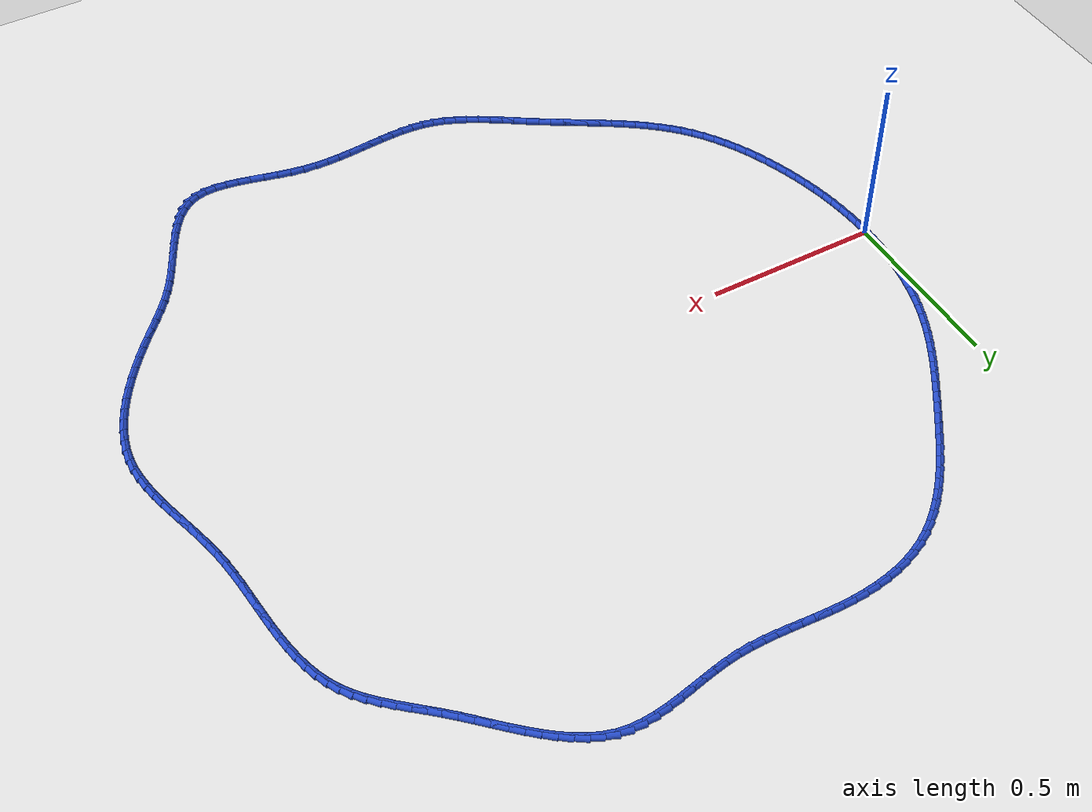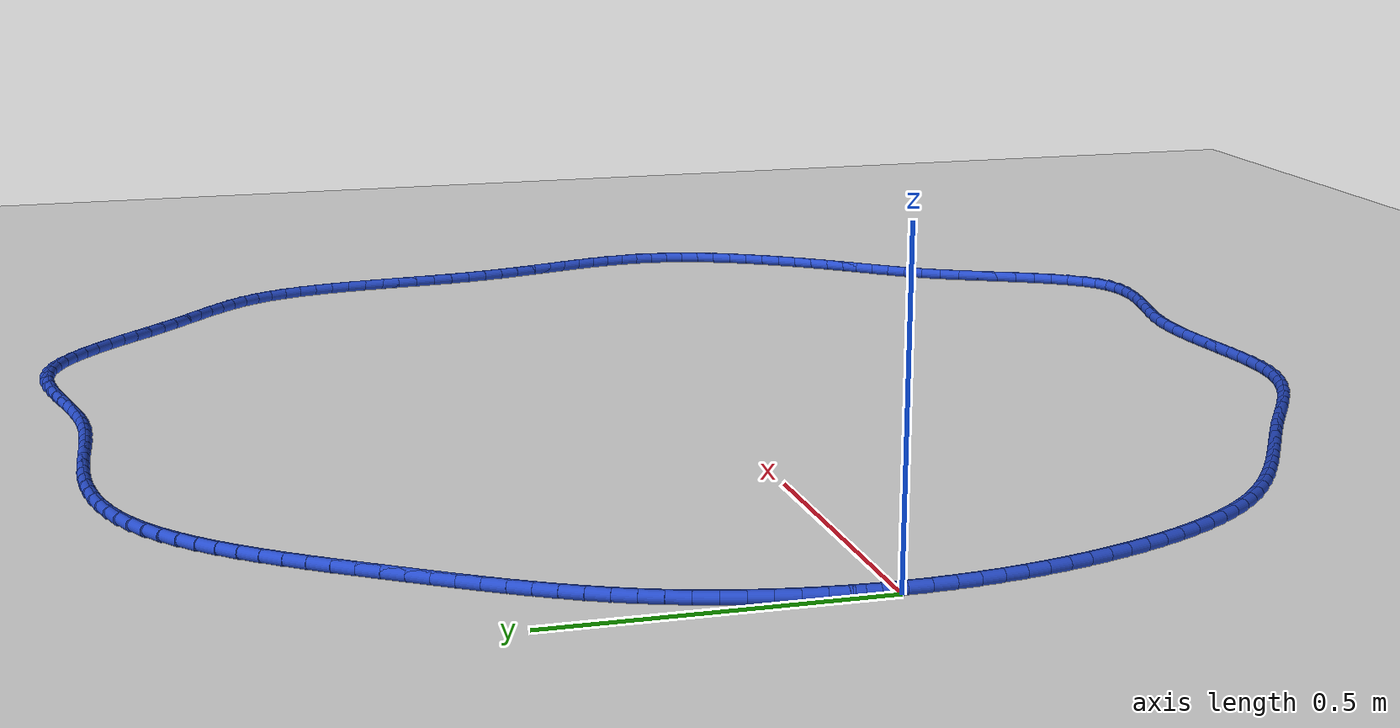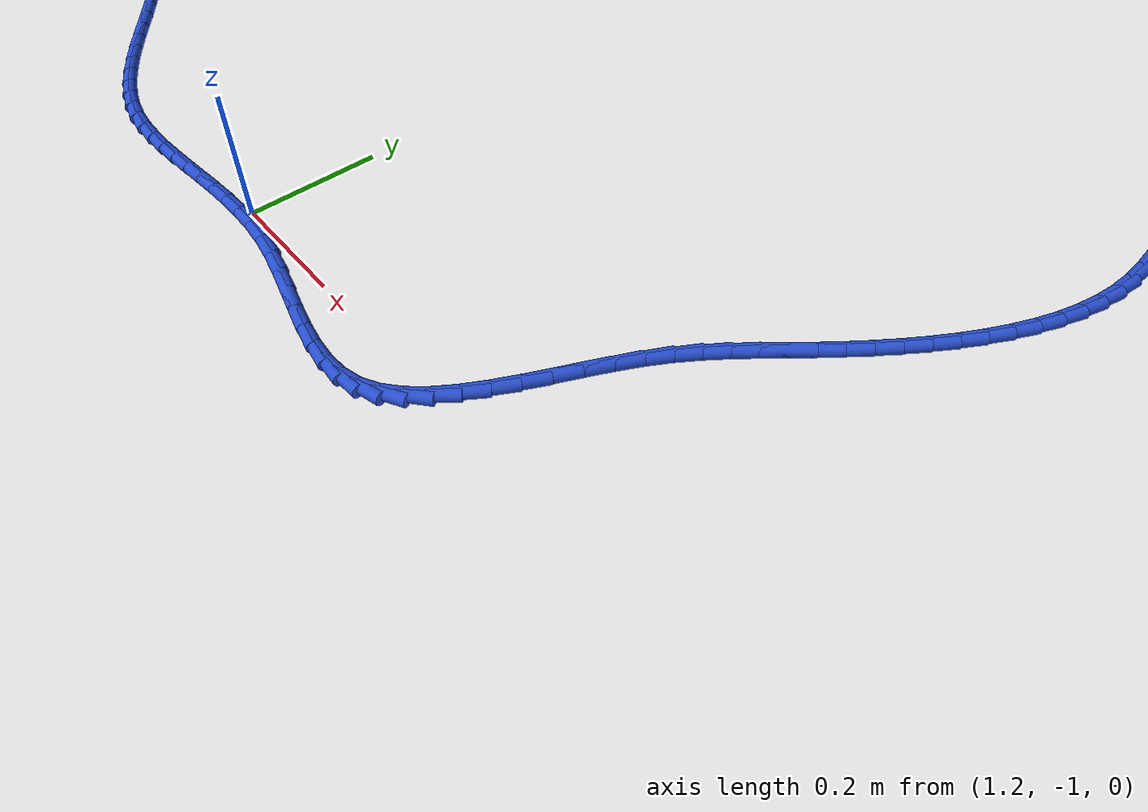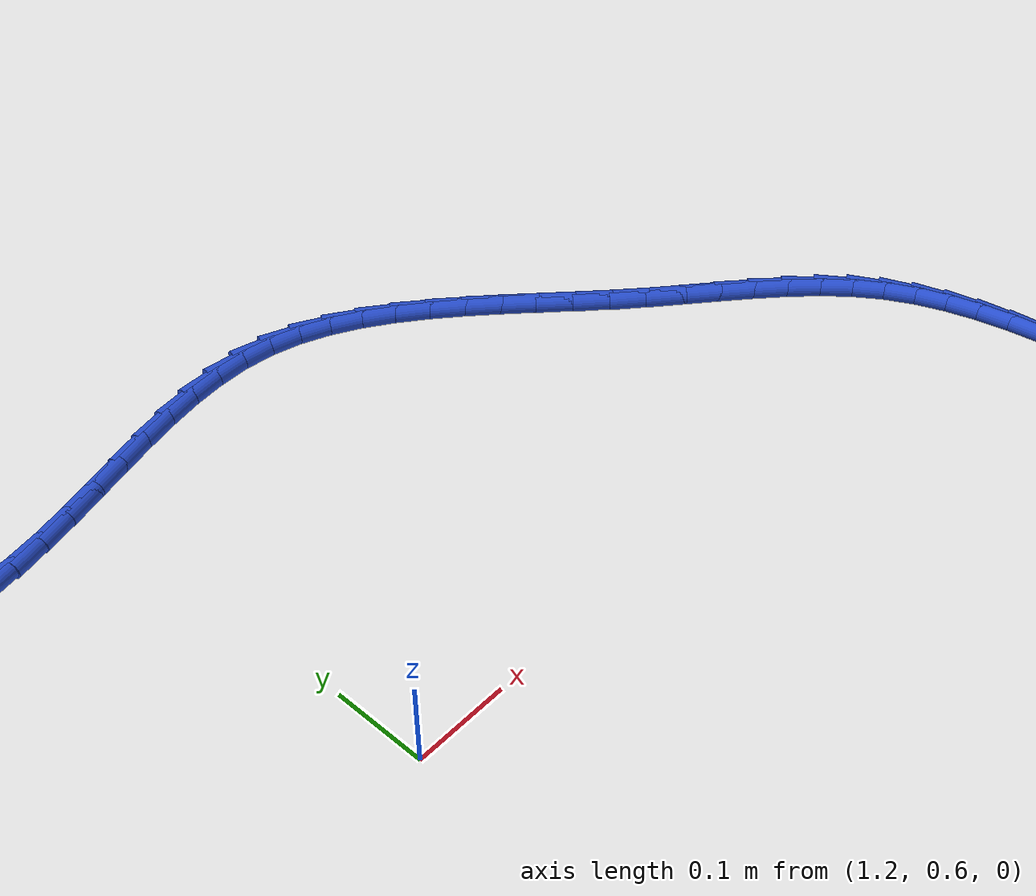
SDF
<sdf version="1.6">
 <world name="default">
  <light name="sun" type="directional">
   <pose>0 0 10 0 -0 0</pose>
   <diffuse>0.8 0.8 0.8 1</diffuse>
   <specular>0.2 0.2 0.2 1</specular>
   <attenuation>
    <range>1000</range>
    <constant>0.9</constant>
    <linear>0.01</linear>
    <quadratic>0.001</quadratic>
   </attenuation>
   <direction>-0.5 0.1 -0.9</direction>
  </light>
  <model name="ground_plane">
   <static>1</static>
   <link name="link">
    <collision name="collision">
     <geometry><plane><normal>0 0 1</normal><size>100 100</size></plane></geometry>
     <surface><friction><ode><mu>100</mu><mu2>50</mu2></ode></friction></surface>
    </collision>
    <visual name="visual">
     <cast_shadows>0</cast_shadows>
     <geometry><plane><normal>0 0 1</normal><size>100 100</size></plane></geometry>
     <material>
      <script><uri>file://media/materials/scripts/gazebo.material</uri><name>Gazebo/WhiteGlow</name></script>
     </material>
    </visual>
   </link>
  </model>
  <gravity>0 0 -9.8</gravity>
  <magnetic_field>6e-06 2.3e-05 -4.2e-05</magnetic_field>
  <atmosphere type="adiabatic"/>
  <physics name="default_physics" default="0" type="ode">
   <max_step_size>0.001</max_step_size>
   <real_time_factor>1</real_time_factor>
   <real_time_update_rate>1000</real_time_update_rate>
  </physics>
  <scene><ambient>0.4 0.4 0.4 1</ambient><background>0.7 0.7 0.7 1</background><shadows>1</shadows></scene>
  <spherical_coordinates>
   <surface_model>EARTH_WGS84</surface_model>
   <latitude_deg>0</latitude_deg>
   <longitude_deg>0</longitude_deg>
   <elevation>0</elevation>
   <heading_deg>0</heading_deg>
  </spherical_coordinates>
  <model name="line">
   <link name="link_0">
    <pose>8.673617379884035e-19 -6.938893903907228e-18 0.01 0 1.57 1.560804196226512</pose>
    <collision name="collision">
     <geometry><cylinder><radius>0.01</radius><length>0.08</length></cylinder></geometry>
    </collision>
    <visual name="visual">
     <material>
      <script><name>Gazebo/Blue</name><uri>file://media/materials/scripts/gazebo.material</uri></script>
     </material>
     <geometry><cylinder><radius>0.01</radius><length>0.08</length></cylinder></geometry>
    </visual>
   </link>
   <link name="link_1">
    <pose>0.00035642979521674603 0.03566986343876464 0.01 0 1.57 1.5253975953398975</pose>
    <collision name="collision">
     <geometry><cylinder><radius>0.01</radius><length>0.08</length></cylinder></geometry>
    </collision>
    <visual name="visual">
     <material>
      <script><name>Gazebo/Blue</name><uri>file://media/materials/scripts/gazebo.material</uri></script>
     </material>
     <geometry><cylinder><radius>0.01</radius><length>0.08</length></cylinder></geometry>
    </visual>
   </link>
   <link name="link_2">
    <pose>0.0019789209129767306 0.07138399546337049 0.01 0 1.57 1.4893793077935327</pose>
    <collision name="collision">
     <geometry><cylinder><radius>0.01</radius><length>0.08</length></cylinder></geometry>
    </collision>
    <visual name="visual">
     <material>
      <script><name>Gazebo/Blue</name><uri>file://media/materials/scripts/gazebo.material</uri></script>
     </material>
     <geometry><cylinder><radius>0.01</radius><length>0.08</length></cylinder></geometry>
    </visual>
   </link>
   <link name="link_3">
    <pose>0.004889206295829885 0.10705039636222353 0.01 0 1.57 1.4525715119699916</pose>
    <collision name="collision">
     <geometry><cylinder><radius>0.01</radius><length>0.08</length></cylinder></geometry>
    </collision>
    <visual name="visual">
     <material>
      <script><name>Gazebo/Blue</name><uri>file://media/materials/scripts/gazebo.material</uri></script>
     </material>
     <geometry><cylinder><radius>0.01</radius><length>0.08</length></cylinder></geometry>
    </visual>
   </link>
   <link name="link_4">
    <pose>0.00910901888632615 0.14257706642372994 0.01 0 1.57 1.4147974794986888</pose>
    <collision name="collision">
     <geometry><cylinder><radius>0.01</radius><length>0.08</length></cylinder></geometry>
    </collision>
    <visual name="visual">
     <material>
      <script><name>Gazebo/Blue</name><uri>file://media/materials/scripts/gazebo.material</uri></script>
     </material>
     <geometry><cylinder><radius>0.01</radius><length>0.08</length></cylinder></geometry>
    </visual>
   </link>
   <link name="link_5">
    <pose>0.014660091627015443 0.17787200593629557 0.01 0 1.57 1.3758813945967248</pose>
    <collision name="collision">
     <geometry><cylinder><radius>0.01</radius><length>0.08</length></cylinder></geometry>
    </collision>
    <visual name="visual">
     <material>
      <script><name>Gazebo/Blue</name><uri>file://media/materials/scripts/gazebo.material</uri></script>
     </material>
     <geometry><cylinder><radius>0.01</radius><length>0.08</length></cylinder></geometry>
    </visual>
   </link>
   <link name="link_6">
    <pose>0.02156415746044771 0.21284321518832658 0.01 0 1.57 1.3356487792455822</pose>
    <collision name="collision">
     <geometry><cylinder><radius>0.01</radius><length>0.08</length></cylinder></geometry>
    </collision>
    <visual name="visual">
     <material>
      <script><name>Gazebo/Blue</name><uri>file://media/materials/scripts/gazebo.material</uri></script>
     </material>
     <geometry><cylinder><radius>0.01</radius><length>0.08</length></cylinder></geometry>
    </visual>
   </link>
   <link name="link_7">
    <pose>0.02984294932917287 0.24739869446822899 0.01 0 1.57 1.2939276528066</pose>
    <collision name="collision">
     <geometry><cylinder><radius>0.01</radius><length>0.08</length></cylinder></geometry>
    </collision>
    <visual name="visual">
     <material>
      <script><name>Gazebo/Blue</name><uri>file://media/materials/scripts/gazebo.material</uri></script>
     </material>
     <geometry><cylinder><radius>0.01</radius><length>0.08</length></cylinder></geometry>
    </visual>
   </link>
   <link name="link_8">
    <pose>0.03951820017574087 0.2814464440644088 0.01 0 1.57 1.250550577946964</pose>
    <collision name="collision">
     <geometry><cylinder><radius>0.01</radius><length>0.08</length></cylinder></geometry>
    </collision>
    <visual name="visual">
     <material>
      <script><name>Gazebo/Blue</name><uri>file://media/materials/scripts/gazebo.material</uri></script>
     </material>
     <geometry><cylinder><radius>0.01</radius><length>0.08</length></cylinder></geometry>
    </visual>
   </link>
   <link name="link_9">
    <pose>0.05061164294270161 0.3148944642652719 0.01 0 1.57 1.2056868077154406</pose>
    <collision name="collision">
     <geometry><cylinder><radius>0.01</radius><length>0.08</length></cylinder></geometry>
    </collision>
    <visual name="visual">
     <material>
      <script><name>Gazebo/Blue</name><uri>file://media/materials/scripts/gazebo.material</uri></script>
     </material>
     <geometry><cylinder><radius>0.01</radius><length>0.08</length></cylinder></geometry>
    </visual>
   </link>
   <link name="link_10">
    <pose>0.06313663496150317 0.3476611653647751 0.01 0 1.57 1.1626769627157991</pose>
    <collision name="collision">
     <geometry><cylinder><radius>0.01</radius><length>0.08</length></cylinder></geometry>
    </collision>
    <visual name="visual">
     <material>
      <script><name>Gazebo/Blue</name><uri>file://media/materials/scripts/gazebo.material</uri></script>
     </material>
     <geometry><cylinder><radius>0.01</radius><length>0.08</length></cylinder></geometry>
    </visual>
   </link>
   <link name="link_11">
    <pose>0.07702096798013851 0.3797713066967087 0.01 0 1.57 1.1237424071856092</pose>
    <collision name="collision">
     <geometry><cylinder><radius>0.01</radius><length>0.08</length></cylinder></geometry>
    </collision>
    <visual name="visual">
     <material>
      <script><name>Gazebo/Blue</name><uri>file://media/materials/scripts/gazebo.material</uri></script>
     </material>
     <geometry><cylinder><radius>0.01</radius><length>0.08</length></cylinder></geometry>
    </visual>
   </link>
   <link name="link_12">
    <pose>0.09214236167289439 0.4113118819272449 0.01 0 1.57 1.089125896518633</pose>
    <collision name="collision">
     <geometry><cylinder><radius>0.01</radius><length>0.08</length></cylinder></geometry>
    </collision>
    <visual name="visual">
     <material>
      <script><name>Gazebo/Blue</name><uri>file://media/materials/scripts/gazebo.material</uri></script>
     </material>
     <geometry><cylinder><radius>0.01</radius><length>0.08</length></cylinder></geometry>
    </visual>
   </link>
   <link name="link_13">
    <pose>0.1083779041406727 0.4423706697019865 0.01 0 1.57 1.0589559659315158</pose>
    <collision name="collision">
     <geometry><cylinder><radius>0.01</radius><length>0.08</length></cylinder></geometry>
    </collision>
    <visual name="visual">
     <material>
      <script><name>Gazebo/Blue</name><uri>file://media/materials/scripts/gazebo.material</uri></script>
     </material>
     <geometry><cylinder><radius>0.01</radius><length>0.08</length></cylinder></geometry>
    </visual>
   </link>
   <link name="link_14">
    <pose>0.1256046834843754 0.4730354486665372 0.01 0 1.57 1.0332889420093587</pose>
    <collision name="collision">
     <geometry><cylinder><radius>0.01</radius><length>0.08</length></cylinder></geometry>
    </collision>
    <visual name="visual">
     <material>
      <script><name>Gazebo/Blue</name><uri>file://media/materials/scripts/gazebo.material</uri></script>
     </material>
     <geometry><cylinder><radius>0.01</radius><length>0.08</length></cylinder></geometry>
    </visual>
   </link>
   <link name="link_15">
    <pose>0.14369978780490453 0.5033939974664999 0.01 0 1.57 1.0121264742219638</pose>
    <collision name="collision">
     <geometry><cylinder><radius>0.01</radius><length>0.08</length></cylinder></geometry>
    </collision>
    <visual name="visual">
     <material>
      <script><name>Gazebo/Blue</name><uri>file://media/materials/scripts/gazebo.material</uri></script>
     </material>
     <geometry><cylinder><radius>0.01</radius><length>0.08</length></cylinder></geometry>
    </visual>
   </link>
   <link name="link_16">
    <pose>0.16254030520316198 0.5335340947474786 0.01 0 1.57 0.9954315816572497</pose>
    <collision name="collision">
     <geometry><cylinder><radius>0.01</radius><length>0.08</length></cylinder></geometry>
    </collision>
    <visual name="visual">
     <material>
      <script><name>Gazebo/Blue</name><uri>file://media/materials/scripts/gazebo.material</uri></script>
     </material>
     <geometry><cylinder><radius>0.01</radius><length>0.08</length></cylinder></geometry>
    </visual>
   </link>
   <link name="link_17">
    <pose>0.18200332378004966 0.5635435191550762 0.01 0 1.57 0.9831421681235767</pose>
    <collision name="collision">
     <geometry><cylinder><radius>0.01</radius><length>0.08</length></cylinder></geometry>
    </collision>
    <visual name="visual">
     <material>
      <script><name>Gazebo/Blue</name><uri>file://media/materials/scripts/gazebo.material</uri></script>
     </material>
     <geometry><cylinder><radius>0.01</radius><length>0.08</length></cylinder></geometry>
    </visual>
   </link>
   <link name="link_18">
    <pose>0.20196593163646953 0.5935100493348956 0.01 0 1.57 0.9751815598811534</pose>
    <collision name="collision">
     <geometry><cylinder><radius>0.01</radius><length>0.08</length></cylinder></geometry>
    </collision>
    <visual name="visual">
     <material>
      <script><name>Gazebo/Blue</name><uri>file://media/materials/scripts/gazebo.material</uri></script>
     </material>
     <geometry><cylinder><radius>0.01</radius><length>0.08</length></cylinder></geometry>
    </visual>
   </link>
   <link name="link_19">
    <pose>0.22230521687332352 0.6235214639325406 0.01 0 1.57 0.9714374148457662</pose>
    <collision name="collision">
     <geometry><cylinder><radius>0.01</radius><length>0.08</length></cylinder></geometry>
    </collision>
    <visual name="visual">
     <material>
      <script><name>Gazebo/Blue</name><uri>file://media/materials/scripts/gazebo.material</uri></script>
     </material>
     <geometry><cylinder><radius>0.01</radius><length>0.08</length></cylinder></geometry>
    </visual>
   </link>
   <link name="link_20">
    <pose>0.2428989312757951 0.6536646616611193 0.01 0 1.57 0.9686889838224352</pose>
    <collision name="collision">
     <geometry><cylinder><radius>0.01</radius><length>0.08</length></cylinder></geometry>
    </collision>
    <visual name="visual">
     <material>
      <script><name>Gazebo/Blue</name><uri>file://media/materials/scripts/gazebo.material</uri></script>
     </material>
     <geometry><cylinder><radius>0.01</radius><length>0.08</length></cylinder></geometry>
    </visual>
   </link>
   <link name="link_21">
    <pose>0.26369800191545556 0.6839295232476775 0.01 0 1.57 0.9609871302476384</pose>
    <collision name="collision">
     <geometry><cylinder><radius>0.01</radius><length>0.08</length></cylinder></geometry>
    </collision>
    <visual name="visual">
     <material>
      <script><name>Gazebo/Blue</name><uri>file://media/materials/scripts/gazebo.material</uri></script>
     </material>
     <geometry><cylinder><radius>0.01</radius><length>0.08</length></cylinder></geometry>
    </visual>
   </link>
   <link name="link_22">
    <pose>0.2847917908375716 0.7141223881854467 0.01 0 1.57 0.9476461623980174</pose>
    <collision name="collision">
     <geometry><cylinder><radius>0.01</radius><length>0.08</length></cylinder></geometry>
    </collision>
    <visual name="visual">
     <material>
      <script><name>Gazebo/Blue</name><uri>file://media/materials/scripts/gazebo.material</uri></script>
     </material>
     <geometry><cylinder><radius>0.01</radius><length>0.08</length></cylinder></geometry>
    </visual>
   </link>
   <link name="link_23">
    <pose>0.30628506323996757 0.7440291740067225 0.01 0 1.57 0.9285466581791092</pose>
    <collision name="collision">
     <geometry><cylinder><radius>0.01</radius><length>0.08</length></cylinder></geometry>
    </collision>
    <visual name="visual">
     <material>
      <script><name>Gazebo/Blue</name><uri>file://media/materials/scripts/gazebo.material</uri></script>
     </material>
     <geometry><cylinder><radius>0.01</radius><length>0.08</length></cylinder></geometry>
    </visual>
   </link>
   <link name="link_24">
    <pose>0.3282825843204676 0.7734357982438003 0.01 0 1.57 0.9034812197182757</pose>
    <collision name="collision">
     <geometry><cylinder><radius>0.01</radius><length>0.08</length></cylinder></geometry>
    </collision>
    <visual name="visual">
     <material>
      <script><name>Gazebo/Blue</name><uri>file://media/materials/scripts/gazebo.material</uri></script>
     </material>
     <geometry><cylinder><radius>0.01</radius><length>0.08</length></cylinder></geometry>
    </visual>
   </link>
   <link name="link_25">
    <pose>0.35088911927689564 0.8021281784289751 0.01 0 1.57 0.8721679899453262</pose>
    <collision name="collision">
     <geometry><cylinder><radius>0.01</radius><length>0.08</length></cylinder></geometry>
    </collision>
    <visual name="visual">
     <material>
      <script><name>Gazebo/Blue</name><uri>file://media/materials/scripts/gazebo.material</uri></script>
     </material>
     <geometry><cylinder><radius>0.01</radius><length>0.08</length></cylinder></geometry>
    </visual>
   </link>
   <link name="link_26">
    <pose>0.37420943330707607 0.8298922320945429 0.01 0 1.57 0.8342709908947274</pose>
    <collision name="collision">
     <geometry><cylinder><radius>0.01</radius><length>0.08</length></cylinder></geometry>
    </collision>
    <visual name="visual">
     <material>
      <script><name>Gazebo/Blue</name><uri>file://media/materials/scripts/gazebo.material</uri></script>
     </material>
     <geometry><cylinder><radius>0.01</radius><length>0.08</length></cylinder></geometry>
    </visual>
   </link>
   <link name="link_27">
    <pose>0.39834829160883267 0.8565138767727982 0.01 0 1.57 0.7894314468583911</pose>
    <collision name="collision">
     <geometry><cylinder><radius>0.01</radius><length>0.08</length></cylinder></geometry>
    </collision>
    <visual name="visual">
     <material>
      <script><name>Gazebo/Blue</name><uri>file://media/materials/scripts/gazebo.material</uri></script>
     </material>
     <geometry><cylinder><radius>0.01</radius><length>0.08</length></cylinder></geometry>
    </visual>
   </link>
   <link name="link_28">
    <pose>0.42341045937999 0.8817790299960372 0.01 0 1.57 0.7373149020363247</pose>
    <collision name="collision">
     <geometry><cylinder><radius>0.01</radius><length>0.08</length></cylinder></geometry>
    </collision>
    <visual name="visual">
     <material>
      <script><name>Gazebo/Blue</name><uri>file://media/materials/scripts/gazebo.material</uri></script>
     </material>
     <geometry><cylinder><radius>0.01</radius><length>0.08</length></cylinder></geometry>
    </visual>
   </link>
   <link name="link_29">
    <pose>0.44950070181837204 0.9054736092965548 0.01 0 1.57 0.6776784548741763</pose>
    <collision name="collision">
     <geometry><cylinder><radius>0.01</radius><length>0.08</length></cylinder></geometry>
    </collision>
    <visual name="visual">
     <material>
      <script><name>Gazebo/Blue</name><uri>file://media/materials/scripts/gazebo.material</uri></script>
     </material>
     <geometry><cylinder><radius>0.01</radius><length>0.08</length></cylinder></geometry>
    </visual>
   </link>
   <link name="link_30">
    <pose>0.4767237841218029 0.9273835322066466 0.01 0 1.57 0.6104595139282976</pose>
    <collision name="collision">
     <geometry><cylinder><radius>0.01</radius><length>0.08</length></cylinder></geometry>
    </collision>
    <visual name="visual">
     <material>
      <script><name>Gazebo/Blue</name><uri>file://media/materials/scripts/gazebo.material</uri></script>
     </material>
     <geometry><cylinder><radius>0.01</radius><length>0.08</length></cylinder></geometry>
    </visual>
   </link>
   <link name="link_31">
    <pose>0.5051844714881066 0.9472947162586077 0.01 0 1.57 0.5358806291473722</pose>
    <collision name="collision">
     <geometry><cylinder><radius>0.01</radius><length>0.08</length></cylinder></geometry>
    </collision>
    <visual name="visual">
     <material>
      <script><name>Gazebo/Blue</name><uri>file://media/materials/scripts/gazebo.material</uri></script>
     </material>
     <geometry><cylinder><radius>0.01</radius><length>0.08</length></cylinder></geometry>
    </visual>
   </link>
   <link name="link_32">
    <pose>0.5349875291151076 0.9649930789847339 0.01 0 1.57 0.45457034131335616</pose>
    <collision name="collision">
     <geometry><cylinder><radius>0.01</radius><length>0.08</length></cylinder></geometry>
    </collision>
    <visual name="visual">
     <material>
      <script><name>Gazebo/Blue</name><uri>file://media/materials/scripts/gazebo.material</uri></script>
     </material>
     <geometry><cylinder><radius>0.01</radius><length>0.08</length></cylinder></geometry>
    </visual>
   </link>
   <link name="link_33">
    <pose>0.5662372657727757 0.9802649619090583 0.01 0 1.57 0.37138330588417057</pose>
    <collision name="collision">
     <geometry><cylinder><radius>0.01</radius><length>0.08</length></cylinder></geometry>
    </collision>
    <visual name="visual">
     <material>
      <script><name>Gazebo/Blue</name><uri>file://media/materials/scripts/gazebo.material</uri></script>
     </material>
     <geometry><cylinder><radius>0.01</radius><length>0.08</length></cylinder></geometry>
    </visual>
   </link>
   <link name="link_34">
    <pose>0.598929770820631 0.9929972353370461 0.01 0 1.57 0.2953534262869572</pose>
    <collision name="collision">
     <geometry><cylinder><radius>0.01</radius><length>0.08</length></cylinder></geometry>
    </collision>
    <visual name="visual">
     <material>
      <script><name>Gazebo/Blue</name><uri>file://media/materials/scripts/gazebo.material</uri></script>
     </material>
     <geometry><cylinder><radius>0.01</radius><length>0.08</length></cylinder></geometry>
    </visual>
   </link>
   <link name="link_35">
    <pose>0.6328137971839443 1.0033065290067344 0.01 0 1.57 0.2269750756102584</pose>
    <collision name="collision">
     <geometry><cylinder><radius>0.01</radius><length>0.08</length></cylinder></geometry>
    </collision>
    <visual name="visual">
     <material>
      <script><name>Gazebo/Blue</name><uri>file://media/materials/scripts/gazebo.material</uri></script>
     </material>
     <geometry><cylinder><radius>0.01</radius><length>0.08</length></cylinder></geometry>
    </visual>
   </link>
   <link name="link_36">
    <pose>0.6676037001206521 1.0113414258479847 0.01 0 1.57 0.16535183219515226</pose>
    <collision name="collision">
     <geometry><cylinder><radius>0.01</radius><length>0.08</length></cylinder></geometry>
    </collision>
    <visual name="visual">
     <material>
      <script><name>Gazebo/Blue</name><uri>file://media/materials/scripts/gazebo.material</uri></script>
     </material>
     <geometry><cylinder><radius>0.01</radius><length>0.08</length></cylinder></geometry>
    </visual>
   </link>
   <link name="link_37">
    <pose>0.7030138348886904 1.017250508790658 0.01 0 1.57 0.10955766288458205</pose>
    <collision name="collision">
     <geometry><cylinder><radius>0.01</radius><length>0.08</length></cylinder></geometry>
    </collision>
    <visual name="visual">
     <material>
      <script><name>Gazebo/Blue</name><uri>file://media/materials/scripts/gazebo.material</uri></script>
     </material>
     <geometry><cylinder><radius>0.01</radius><length>0.08</length></cylinder></geometry>
    </visual>
   </link>
   <link name="link_38">
    <pose>0.7387585567459962 1.0211823607646158 0.01 0 1.57 0.058691627503041396</pose>
    <collision name="collision">
     <geometry><cylinder><radius>0.01</radius><length>0.08</length></cylinder></geometry>
    </collision>
    <visual name="visual">
     <material>
      <script><name>Gazebo/Blue</name><uri>file://media/materials/scripts/gazebo.material</uri></script>
     </material>
     <geometry><cylinder><radius>0.01</radius><length>0.08</length></cylinder></geometry>
    </visual>
   </link>
   <link name="link_39">
    <pose>0.7745522209505062 1.0232855646997197 0.01 0 1.57 0.012994231476737244</pose>
    <collision name="collision">
     <geometry><cylinder><radius>0.01</radius><length>0.08</length></cylinder></geometry>
    </collision>
    <visual name="visual">
     <material>
      <script><name>Gazebo/Blue</name><uri>file://media/materials/scripts/gazebo.material</uri></script>
     </material>
     <geometry><cylinder><radius>0.01</radius><length>0.08</length></cylinder></geometry>
    </visual>
   </link>
   <link name="link_40">
    <pose>0.8101576348989149 1.023748255732485 0.01 0 1.57 -0.022651811205012303</pose>
    <collision name="collision">
     <geometry><cylinder><radius>0.01</radius><length>0.08</length></cylinder></geometry>
    </collision>
    <visual name="visual">
     <material>
      <script><name>Gazebo/Blue</name><uri>file://media/materials/scripts/gazebo.material</uri></script>
     </material>
     <geometry><cylinder><radius>0.01</radius><length>0.08</length></cylinder></geometry>
    </visual>
   </link>
   <link name="link_41">
    <pose>0.8455672449415528 1.0229460267171429 0.01 0 1.57 -0.04634842842652508</pose>
    <collision name="collision">
     <geometry><cylinder><radius>0.01</radius><length>0.08</length></cylinder></geometry>
    </collision>
    <visual name="visual">
     <material>
      <script><name>Gazebo/Blue</name><uri>file://media/materials/scripts/gazebo.material</uri></script>
     </material>
     <geometry><cylinder><radius>0.01</radius><length>0.08</length></cylinder></geometry>
    </visual>
   </link>
   <link name="link_42">
    <pose>0.8808414614113669 1.0213099505249965 0.01 0 1.57 -0.05785824511243321</pose>
    <collision name="collision">
     <geometry><cylinder><radius>0.01</radius><length>0.08</length></cylinder></geometry>
    </collision>
    <visual name="visual">
     <material>
      <script><name>Gazebo/Blue</name><uri>file://media/materials/scripts/gazebo.material</uri></script>
     </material>
     <geometry><cylinder><radius>0.01</radius><length>0.08</length></cylinder></geometry>
    </visual>
   </link>
   <link name="link_43">
    <pose>0.9160407050120856 1.0192711084931732 0.01 0 1.57 -0.05708001010434795</pose>
    <collision name="collision">
     <geometry><cylinder><radius>0.01</radius><length>0.08</length></cylinder></geometry>
    </collision>
    <visual name="visual">
     <material>
      <script><name>Gazebo/Blue</name><uri>file://media/materials/scripts/gazebo.material</uri></script>
     </material>
     <geometry><cylinder><radius>0.01</radius><length>0.08</length></cylinder></geometry>
    </visual>
   </link>
   <link name="link_44">
    <pose>0.9512253964474364 1.0172605819587996 0.01 0 1.57 -0.043999544621473125</pose>
    <collision name="collision">
     <geometry><cylinder><radius>0.01</radius><length>0.08</length></cylinder></geometry>
    </collision>
    <visual name="visual">
     <material>
      <script><name>Gazebo/Blue</name><uri>file://media/materials/scripts/gazebo.material</uri></script>
     </material>
     <geometry><cylinder><radius>0.01</radius><length>0.08</length></cylinder></geometry>
    </visual>
   </link>
   <link name="link_45">
    <pose>0.986455956421148 1.015709452259003 0.01 0 1.57 -0.018693646590850137</pose>
    <collision name="collision">
     <geometry><cylinder><radius>0.01</radius><length>0.08</length></cylinder></geometry>
    </collision>
    <visual name="visual">
     <material>
      <script><name>Gazebo/Blue</name><uri>file://media/materials/scripts/gazebo.material</uri></script>
     </material>
     <geometry><cylinder><radius>0.01</radius><length>0.08</length></cylinder></geometry>
    </visual>
   </link>
   <link name="link_46">
    <pose>1.0217928056369476 1.0150488007309102 0.01 0 1.57 0.018613110099203824</pose>
    <collision name="collision">
     <geometry><cylinder><radius>0.01</radius><length>0.08</length></cylinder></geometry>
    </collision>
    <visual name="visual">
     <material>
      <script><name>Gazebo/Blue</name><uri>file://media/materials/scripts/gazebo.material</uri></script>
     </material>
     <geometry><cylinder><radius>0.01</radius><length>0.08</length></cylinder></geometry>
    </visual>
   </link>
   <link name="link_47">
    <pose>1.0572963647985636 1.0157097087116487 0.01 0 1.57 0.0674458855068575</pose>
    <collision name="collision">
     <geometry><cylinder><radius>0.01</radius><length>0.08</length></cylinder></geometry>
    </collision>
    <visual name="visual">
     <material>
      <script><name>Gazebo/Blue</name><uri>file://media/materials/scripts/gazebo.material</uri></script>
     </material>
     <geometry><cylinder><radius>0.01</radius><length>0.08</length></cylinder></geometry>
    </visual>
   </link>
   <link name="link_48">
    <pose>1.0930270546097247 1.018123257538345 0.01 0 1.57 0.1257058451458308</pose>
    <collision name="collision">
     <geometry><cylinder><radius>0.01</radius><length>0.08</length></cylinder></geometry>
    </collision>
    <visual name="visual">
     <material>
      <script><name>Gazebo/Blue</name><uri>file://media/materials/scripts/gazebo.material</uri></script>
     </material>
     <geometry><cylinder><radius>0.01</radius><length>0.08</length></cylinder></geometry>
    </visual>
   </link>
   <link name="link_49">
    <pose>1.129036618281931 1.0226738649669316 0.01 0 1.57 0.17567723894438655</pose>
    <collision name="collision">
     <geometry><cylinder><radius>0.01</radius><length>0.08</length></cylinder></geometry>
    </collision>
    <visual name="visual">
     <material>
      <script><name>Gazebo/Blue</name><uri>file://media/materials/scripts/gazebo.material</uri></script>
     </material>
     <geometry><cylinder><radius>0.01</radius><length>0.08</length></cylinder></geometry>
    </visual>
   </link>
   <link name="link_50">
    <pose>1.1652572915109904 1.029103292036805 0.01 0 1.57 0.20604356557983597</pose>
    <collision name="collision">
     <geometry><cylinder><radius>0.01</radius><length>0.08</length></cylinder></geometry>
    </collision>
    <visual name="visual">
     <material>
      <script><name>Gazebo/Blue</name><uri>file://media/materials/scripts/gazebo.material</uri></script>
     </material>
     <geometry><cylinder><radius>0.01</radius><length>0.08</length></cylinder></geometry>
    </visual>
   </link>
   <link name="link_51">
    <pose>1.201534327096754 1.0366855455881054 0.01 0 1.57 0.21759530469358354</pose>
    <collision name="collision">
     <geometry><cylinder><radius>0.01</radius><length>0.08</length></cylinder></geometry>
    </collision>
    <visual name="visual">
     <material>
      <script><name>Gazebo/Blue</name><uri>file://media/materials/scripts/gazebo.material</uri></script>
     </material>
     <geometry><cylinder><radius>0.01</radius><length>0.08</length></cylinder></geometry>
    </visual>
   </link>
   <link name="link_52">
    <pose>1.23771101174525 1.0446840597083418 0.01 0 1.57 0.21059146274823012</pose>
    <collision name="collision">
     <geometry><cylinder><radius>0.01</radius><length>0.08</length></cylinder></geometry>
    </collision>
    <visual name="visual">
     <material>
      <script><name>Gazebo/Blue</name><uri>file://media/materials/scripts/gazebo.material</uri></script>
     </material>
     <geometry><cylinder><radius>0.01</radius><length>0.08</length></cylinder></geometry>
    </visual>
   </link>
   <link name="link_53">
    <pose>1.2736306321625064 1.0523622684850245 0.01 0 1.57 0.18436806937053457</pose>
    <collision name="collision">
     <geometry><cylinder><radius>0.01</radius><length>0.08</length></cylinder></geometry>
    </collision>
    <visual name="visual">
     <material>
      <script><name>Gazebo/Blue</name><uri>file://media/materials/scripts/gazebo.material</uri></script>
     </material>
     <geometry><cylinder><radius>0.01</radius><length>0.08</length></cylinder></geometry>
    </visual>
   </link>
   <link name="link_54">
    <pose>1.3091364750545527 1.0589836060056632 0.01 0 1.57 0.137325465639768</pose>
    <collision name="collision">
     <geometry><cylinder><radius>0.01</radius><length>0.08</length></cylinder></geometry>
    </collision>
    <visual name="visual">
     <material>
      <script><name>Gazebo/Blue</name><uri>file://media/materials/scripts/gazebo.material</uri></script>
     </material>
     <geometry><cylinder><radius>0.01</radius><length>0.08</length></cylinder></geometry>
    </visual>
   </link>
   <link name="link_55">
    <pose>1.344071827127416 1.0638115063577673 0.01 0 1.57 0.06707321019510204</pose>
    <collision name="collision">
     <geometry><cylinder><radius>0.01</radius><length>0.08</length></cylinder></geometry>
    </collision>
    <visual name="visual">
     <material>
      <script><name>Gazebo/Blue</name><uri>file://media/materials/scripts/gazebo.material</uri></script>
     </material>
     <geometry><cylinder><radius>0.01</radius><length>0.08</length></cylinder></geometry>
    </visual>
   </link>
   <link name="link_56">
    <pose>1.3782799750871249 1.0661094036288465 0.01 0 1.57 -0.029059906769959794</pose>
    <collision name="collision">
     <geometry><cylinder><radius>0.01</radius><length>0.08</length></cylinder></geometry>
    </collision>
    <visual name="visual">
     <material>
      <script><name>Gazebo/Blue</name><uri>file://media/materials/scripts/gazebo.material</uri></script>
     </material>
     <geometry><cylinder><radius>0.01</radius><length>0.08</length></cylinder></geometry>
    </visual>
   </link>
   <link name="link_57">
    <pose>1.4116042056397082 1.0651407319064106 0.01 0 1.57 -0.1527414919998399</pose>
    <collision name="collision">
     <geometry><cylinder><radius>0.01</radius><length>0.08</length></cylinder></geometry>
    </collision>
    <visual name="visual">
     <material>
      <script><name>Gazebo/Blue</name><uri>file://media/materials/scripts/gazebo.material</uri></script>
     </material>
     <geometry><cylinder><radius>0.01</radius><length>0.08</length></cylinder></geometry>
    </visual>
   </link>
   <link name="link_58">
    <pose>1.4438882835481863 1.0601709048054642 0.01 0 1.57 -0.2911331496929525</pose>
    <collision name="collision">
     <geometry><cylinder><radius>0.01</radius><length>0.08</length></cylinder></geometry>
    </collision>
    <visual name="visual">
     <material>
      <script><name>Gazebo/Blue</name><uri>file://media/materials/scripts/gazebo.material</uri></script>
     </material>
     <geometry><cylinder><radius>0.01</radius><length>0.08</length></cylinder></geometry>
    </visual>
   </link>
   <link name="link_59">
    <pose>1.4750638542922023 1.0508292304087916 0.01 0 1.57 -0.41492777400528913</pose>
    <collision name="collision">
     <geometry><cylinder><radius>0.01</radius><length>0.08</length></cylinder></geometry>
    </collision>
    <visual name="visual">
     <material>
      <script><name>Gazebo/Blue</name><uri>file://media/materials/scripts/gazebo.material</uri></script>
     </material>
     <geometry><cylinder><radius>0.01</radius><length>0.08</length></cylinder></geometry>
    </visual>
   </link>
   <link name="link_60">
    <pose>1.5052524028665686 1.0375310999353935 0.01 0 1.57 -0.5182870962613952</pose>
    <collision name="collision">
     <geometry><cylinder><radius>0.01</radius><length>0.08</length></cylinder></geometry>
    </collision>
    <visual name="visual">
     <material>
      <script><name>Gazebo/Blue</name><uri>file://media/materials/scripts/gazebo.material</uri></script>
     </material>
     <geometry><cylinder><radius>0.01</radius><length>0.08</length></cylinder></geometry>
    </visual>
   </link>
   <link name="link_61">
    <pose>1.5346001616126972 1.0207943778528599 0.01 0 1.57 -0.6013001775073027</pose>
    <collision name="collision">
     <geometry><cylinder><radius>0.01</radius><length>0.08</length></cylinder></geometry>
    </collision>
    <visual name="visual">
     <material>
      <script><name>Gazebo/Blue</name><uri>file://media/materials/scripts/gazebo.material</uri></script>
     </material>
     <geometry><cylinder><radius>0.01</radius><length>0.08</length></cylinder></geometry>
    </visual>
   </link>
   <link name="link_62">
    <pose>1.563253362872003 1.0011369286287812 0.01 0 1.57 -0.6654830634347446</pose>
    <collision name="collision">
     <geometry><cylinder><radius>0.01</radius><length>0.08</length></cylinder></geometry>
    </collision>
    <visual name="visual">
     <material>
      <script><name>Gazebo/Blue</name><uri>file://media/materials/scripts/gazebo.material</uri></script>
     </material>
     <geometry><cylinder><radius>0.01</radius><length>0.08</length></cylinder></geometry>
    </visual>
   </link>
   <link name="link_63">
    <pose>1.5913582389858982 0.9790766167307475 0.01 0 1.57 -0.7127746688904026</pose>
    <collision name="collision">
     <geometry><cylinder><radius>0.01</radius><length>0.08</length></cylinder></geometry>
    </collision>
    <visual name="visual">
     <material>
      <script><name>Gazebo/Blue</name><uri>file://media/materials/scripts/gazebo.material</uri></script>
     </material>
     <geometry><cylinder><radius>0.01</radius><length>0.08</length></cylinder></geometry>
    </visual>
   </link>
   <link name="link_64">
    <pose>1.6190610222957975 0.9551313066263486 0.01 0 1.57 -0.7449633413365636</pose>
    <collision name="collision">
     <geometry><cylinder><radius>0.01</radius><length>0.08</length></cylinder></geometry>
    </collision>
    <visual name="visual">
     <material>
      <script><name>Gazebo/Blue</name><uri>file://media/materials/scripts/gazebo.material</uri></script>
     </material>
     <geometry><cylinder><radius>0.01</radius><length>0.08</length></cylinder></geometry>
    </visual>
   </link>
   <link name="link_65">
    <pose>1.6465079451431135 0.9298188627831747 0.01 0 1.57 -0.7634278035094564</pose>
    <collision name="collision">
     <geometry><cylinder><radius>0.01</radius><length>0.08</length></cylinder></geometry>
    </collision>
    <visual name="visual">
     <material>
      <script><name>Gazebo/Blue</name><uri>file://media/materials/scripts/gazebo.material</uri></script>
     </material>
     <geometry><cylinder><radius>0.01</radius><length>0.08</length></cylinder></geometry>
    </visual>
   </link>
   <link name="link_66">
    <pose>1.6738452398692591 0.903657149668816 0.01 0 1.57 -0.769048593693398</pose>
    <collision name="collision">
     <geometry><cylinder><radius>0.01</radius><length>0.08</length></cylinder></geometry>
    </collision>
    <visual name="visual">
     <material>
      <script><name>Gazebo/Blue</name><uri>file://media/materials/scripts/gazebo.material</uri></script>
     </material>
     <geometry><cylinder><radius>0.01</radius><length>0.08</length></cylinder></geometry>
    </visual>
   </link>
   <link name="link_67">
    <pose>1.7012191388156488 0.8771640317508623 0.01 0 1.57 -0.7621940390661649</pose>
    <collision name="collision">
     <geometry><cylinder><radius>0.01</radius><length>0.08</length></cylinder></geometry>
    </collision>
    <visual name="visual">
     <material>
      <script><name>Gazebo/Blue</name><uri>file://media/materials/scripts/gazebo.material</uri></script>
     </material>
     <geometry><cylinder><radius>0.01</radius><length>0.08</length></cylinder></geometry>
    </visual>
   </link>
   <link name="link_68">
    <pose>1.7287758743236958 0.8508573734969038 0.01 0 1.57 -0.7427766465327265</pose>
    <collision name="collision">
     <geometry><cylinder><radius>0.01</radius><length>0.08</length></cylinder></geometry>
    </collision>
    <visual name="visual">
     <material>
      <script><name>Gazebo/Blue</name><uri>file://media/materials/scripts/gazebo.material</uri></script>
     </material>
     <geometry><cylinder><radius>0.01</radius><length>0.08</length></cylinder></geometry>
    </visual>
   </link>
   <link name="link_69">
    <pose>1.7566607033302541 0.8252536876010425 0.01 0 1.57 -0.7189328287618874</pose>
    <collision name="collision">
     <geometry><cylinder><radius>0.01</radius><length>0.08</length></cylinder></geometry>
    </collision>
    <visual name="visual">
     <material>
      <script><name>Gazebo/Blue</name><uri>file://media/materials/scripts/gazebo.material</uri></script>
     </material>
     <geometry><cylinder><radius>0.01</radius><length>0.08</length></cylinder></geometry>
    </visual>
   </link>
   <link name="link_70">
    <pose>1.784826778648616 0.8006032574694278 0.01 0 1.57 -0.709641354633956</pose>
    <collision name="collision">
     <geometry><cylinder><radius>0.01</radius><length>0.08</length></cylinder></geometry>
    </collision>
    <visual name="visual">
     <material>
      <script><name>Gazebo/Blue</name><uri>file://media/materials/scripts/gazebo.material</uri></script>
     </material>
     <geometry><cylinder><radius>0.01</radius><length>0.08</length></cylinder></geometry>
    </visual>
   </link>
   <link name="link_71">
    <pose>1.8128056384524904 0.7765720679350939 0.01 0 1.57 -0.7180971233676402</pose>
    <collision name="collision">
     <geometry><cylinder><radius>0.01</radius><length>0.08</length></cylinder></geometry>
    </collision>
    <visual name="visual">
     <material>
      <script><name>Gazebo/Blue</name><uri>file://media/materials/scripts/gazebo.material</uri></script>
     </material>
     <geometry><cylinder><radius>0.01</radius><length>0.08</length></cylinder></geometry>
    </visual>
   </link>
   <link name="link_72">
    <pose>1.8400728422825565 0.7527485253213826 0.01 0 1.57 -0.7453940636594112</pose>
    <collision name="collision">
     <geometry><cylinder><radius>0.01</radius><length>0.08</length></cylinder></geometry>
    </collision>
    <visual name="visual">
     <material>
      <script><name>Gazebo/Blue</name><uri>file://media/materials/scripts/gazebo.material</uri></script>
     </material>
     <geometry><cylinder><radius>0.01</radius><length>0.08</length></cylinder></geometry>
    </visual>
   </link>
   <link name="link_73">
    <pose>1.866103949679493 0.7287210359516352 0.01 0 1.57 -0.793012652969606</pose>
    <collision name="collision">
     <geometry><cylinder><radius>0.01</radius><length>0.08</length></cylinder></geometry>
    </collision>
    <visual name="visual">
     <material>
      <script><name>Gazebo/Blue</name><uri>file://media/materials/scripts/gazebo.material</uri></script>
     </material>
     <geometry><cylinder><radius>0.01</radius><length>0.08</length></cylinder></geometry>
    </visual>
   </link>
   <link name="link_74">
    <pose>1.8903745201839806 0.7040780061491931 0.01 0 1.57 -0.8625610352688857</pose>
    <collision name="collision">
     <geometry><cylinder><radius>0.01</radius><length>0.08</length></cylinder></geometry>
    </collision>
    <visual name="visual">
     <material>
      <script><name>Gazebo/Blue</name><uri>file://media/materials/scripts/gazebo.material</uri></script>
     </material>
     <geometry><cylinder><radius>0.01</radius><length>0.08</length></cylinder></geometry>
    </visual>
   </link>
   <link name="link_75">
    <pose>1.9123601133366974 0.6784078422373974 0.01 0 1.57 -0.9550703370006088</pose>
    <collision name="collision">
     <geometry><cylinder><radius>0.01</radius><length>0.08</length></cylinder></geometry>
    </collision>
    <visual name="visual">
     <material>
      <script><name>Gazebo/Blue</name><uri>file://media/materials/scripts/gazebo.material</uri></script>
     </material>
     <geometry><cylinder><radius>0.01</radius><length>0.08</length></cylinder></geometry>
    </visual>
   </link>
   <link name="link_76">
    <pose>1.9315381468479251 0.6513001717759448 0.01 0 1.57 -1.060467227652324</pose>
    <collision name="collision">
     <geometry><cylinder><radius>0.01</radius><length>0.08</length></cylinder></geometry>
    </collision>
    <visual name="visual">
     <material>
      <script><name>Gazebo/Blue</name><uri>file://media/materials/scripts/gazebo.material</uri></script>
     </material>
     <geometry><cylinder><radius>0.01</radius><length>0.08</length></cylinder></geometry>
    </visual>
   </link>
   <link name="link_77">
    <pose>1.9476500622085606 0.6225181454728663 0.01 0 1.57 -1.1570530969371684</pose>
    <collision name="collision">
     <geometry><cylinder><radius>0.01</radius><length>0.08</length></cylinder></geometry>
    </collision>
    <visual name="visual">
     <material>
      <script><name>Gazebo/Blue</name><uri>file://media/materials/scripts/gazebo.material</uri></script>
     </material>
     <geometry><cylinder><radius>0.01</radius><length>0.08</length></cylinder></geometry>
    </visual>
   </link>
   <link name="link_78">
    <pose>1.9609726311764195 0.5921767467123961 0.01 0 1.57 -1.2407419334439116</pose>
    <collision name="collision">
     <geometry><cylinder><radius>0.01</radius><length>0.08</length></cylinder></geometry>
    </collision>
    <visual name="visual">
     <material>
      <script><name>Gazebo/Blue</name><uri>file://media/materials/scripts/gazebo.material</uri></script>
     </material>
     <geometry><cylinder><radius>0.01</radius><length>0.08</length></cylinder></geometry>
    </visual>
   </link>
   <link name="link_79">
    <pose>1.9718474011377136 0.5604335310703656 0.01 0 1.57 -1.310990582640275</pose>
    <collision name="collision">
     <geometry><cylinder><radius>0.01</radius><length>0.08</length></cylinder></geometry>
    </collision>
    <visual name="visual">
     <material>
      <script><name>Gazebo/Blue</name><uri>file://media/materials/scripts/gazebo.material</uri></script>
     </material>
     <geometry><cylinder><radius>0.01</radius><length>0.08</length></cylinder></geometry>
    </visual>
   </link>
   <link name="link_80">
    <pose>1.9806159194786548 0.5274460541226066 0.01 0 1.57 -1.368073745830297</pose>
    <collision name="collision">
     <geometry><cylinder><radius>0.01</radius><length>0.08</length></cylinder></geometry>
    </collision>
    <visual name="visual">
     <material>
      <script><name>Gazebo/Blue</name><uri>file://media/materials/scripts/gazebo.material</uri></script>
     </material>
     <geometry><cylinder><radius>0.01</radius><length>0.08</length></cylinder></geometry>
    </visual>
   </link>
   <link name="link_81">
    <pose>1.9876197335854549 0.4933718714449497 0.01 0 1.57 -1.4126947714392184</pose>
    <collision name="collision">
     <geometry><cylinder><radius>0.01</radius><length>0.08</length></cylinder></geometry>
    </collision>
    <visual name="visual">
     <material>
      <script><name>Gazebo/Blue</name><uri>file://media/materials/scripts/gazebo.material</uri></script>
     </material>
     <geometry><cylinder><radius>0.01</radius><length>0.08</length></cylinder></geometry>
    </visual>
   </link>
   <link name="link_82">
    <pose>1.9932003908443252 0.45836853861322663 0.01 0 1.57 -1.445693289339995</pose>
    <collision name="collision">
     <geometry><cylinder><radius>0.01</radius><length>0.08</length></cylinder></geometry>
    </collision>
    <visual name="visual">
     <material>
      <script><name>Gazebo/Blue</name><uri>file://media/materials/scripts/gazebo.material</uri></script>
     </material>
     <geometry><cylinder><radius>0.01</radius><length>0.08</length></cylinder></geometry>
    </visual>
   </link>
   <link name="link_83">
    <pose>1.997699438641478 0.42259361120326927 0.01 0 1.57 -1.4678612770690267</pose>
    <collision name="collision">
     <geometry><cylinder><radius>0.01</radius><length>0.08</length></cylinder></geometry>
    </collision>
    <visual name="visual">
     <material>
      <script><name>Gazebo/Blue</name><uri>file://media/materials/scripts/gazebo.material</uri></script>
     </material>
     <geometry><cylinder><radius>0.01</radius><length>0.08</length></cylinder></geometry>
    </visual>
   </link>
   <link name="link_84">
    <pose>2.001458424363125 0.3862046447909082 0.01 0 1.57 -1.4798434542501462</pose>
    <collision name="collision">
     <geometry><cylinder><radius>0.01</radius><length>0.08</length></cylinder></geometry>
    </collision>
    <visual name="visual">
     <material>
      <script><name>Gazebo/Blue</name><uri>file://media/materials/scripts/gazebo.material</uri></script>
     </material>
     <geometry><cylinder><radius>0.01</radius><length>0.08</length></cylinder></geometry>
    </visual>
   </link>
   <link name="link_85">
    <pose>2.0048188953954775 0.3493591949519752 0.01 0 1.57 -1.4820928658127737</pose>
    <collision name="collision">
     <geometry><cylinder><radius>0.01</radius><length>0.08</length></cylinder></geometry>
    </collision>
    <visual name="visual">
     <material>
      <script><name>Gazebo/Blue</name><uri>file://media/materials/scripts/gazebo.material</uri></script>
     </material>
     <geometry><cylinder><radius>0.01</radius><length>0.08</length></cylinder></geometry>
    </visual>
   </link>
   <link name="link_86">
    <pose>2.0081223991247477 0.3122148172623018 0.01 0 1.57 -1.4748597019320595</pose>
    <collision name="collision">
     <geometry><cylinder><radius>0.01</radius><length>0.08</length></cylinder></geometry>
    </collision>
    <visual name="visual">
     <material>
      <script><name>Gazebo/Blue</name><uri>file://media/materials/scripts/gazebo.material</uri></script>
     </material>
     <geometry><cylinder><radius>0.01</radius><length>0.08</length></cylinder></geometry>
    </visual>
   </link>
   <link name="link_87">
    <pose>2.0117104829371475 0.27492906729771893 0.01 0 1.57 -1.458200778438653</pose>
    <collision name="collision">
     <geometry><cylinder><radius>0.01</radius><length>0.08</length></cylinder></geometry>
    </collision>
    <visual name="visual">
     <material>
      <script><name>Gazebo/Blue</name><uri>file://media/materials/scripts/gazebo.material</uri></script>
     </material>
     <geometry><cylinder><radius>0.01</radius><length>0.08</length></cylinder></geometry>
    </visual>
   </link>
   <link name="link_88">
    <pose>2.015924694218888 0.23765950063405814 0.01 0 1.57 -1.4320052335068707</pose>
    <collision name="collision">
     <geometry><cylinder><radius>0.01</radius><length>0.08</length></cylinder></geometry>
    </collision>
    <visual name="visual">
     <material>
      <script><name>Gazebo/Blue</name><uri>file://media/materials/scripts/gazebo.material</uri></script>
     </material>
     <geometry><cylinder><radius>0.01</radius><length>0.08</length></cylinder></geometry>
    </visual>
   </link>
   <link name="link_89">
    <pose>2.0211065803561823 0.20056367284715093 0.01 0 1.57 -1.3960385786762433</pose>
    <collision name="collision">
     <geometry><cylinder><radius>0.01</radius><length>0.08</length></cylinder></geometry>
    </collision>
    <visual name="visual">
     <material>
      <script><name>Gazebo/Blue</name><uri>file://media/materials/scripts/gazebo.material</uri></script>
     </material>
     <geometry><cylinder><radius>0.01</radius><length>0.08</length></cylinder></geometry>
    </visual>
   </link>
   <link name="link_90">
    <pose>2.0275976826189246 0.16379913798144463 0.01 0 1.57 -1.3540749856608922</pose>
    <collision name="collision">
     <geometry><cylinder><radius>0.01</radius><length>0.08</length></cylinder></geometry>
    </collision>
    <visual name="visual">
     <material>
      <script><name>Gazebo/Blue</name><uri>file://media/materials/scripts/gazebo.material</uri></script>
     </material>
     <geometry><cylinder><radius>0.01</radius><length>0.08</length></cylinder></geometry>
    </visual>
   </link>
   <link name="link_91">
    <pose>2.03559292181869 0.12748673969909746 0.01 0 1.57 -1.3205813483886362</pose>
    <collision name="collision">
     <geometry><cylinder><radius>0.01</radius><length>0.08</length></cylinder></geometry>
    </collision>
    <visual name="visual">
     <material>
      <script><name>Gazebo/Blue</name><uri>file://media/materials/scripts/gazebo.material</uri></script>
     </material>
     <geometry><cylinder><radius>0.01</radius><length>0.08</length></cylinder></geometry>
    </visual>
   </link>
   <link name="link_92">
    <pose>2.044760577369315 0.09161546279849983 0.01 0 1.57 -1.2988771034930866</pose>
    <collision name="collision">
     <geometry><cylinder><radius>0.01</radius><length>0.08</length></cylinder></geometry>
    </collision>
    <visual name="visual">
     <material>
      <script><name>Gazebo/Blue</name><uri>file://media/materials/scripts/gazebo.material</uri></script>
     </material>
     <geometry><cylinder><radius>0.01</radius><length>0.08</length></cylinder></geometry>
    </visual>
   </link>
   <link name="link_93">
    <pose>2.0546507298339844 0.05614469781102788 0.01 0 1.57 -1.2890491829731943</pose>
    <collision name="collision">
     <geometry><cylinder><radius>0.01</radius><length>0.08</length></cylinder></geometry>
    </collision>
    <visual name="visual">
     <material>
      <script><name>Gazebo/Blue</name><uri>file://media/materials/scripts/gazebo.material</uri></script>
     </material>
     <geometry><cylinder><radius>0.01</radius><length>0.08</length></cylinder></geometry>
    </visual>
   </link>
   <link name="link_94">
    <pose>2.064813459775885 0.021033835268056515 0.01 0 1.57 -1.2913028820206467</pose>
    <collision name="collision">
     <geometry><cylinder><radius>0.01</radius><length>0.08</length></cylinder></geometry>
    </collision>
    <visual name="visual">
     <material>
      <script><name>Gazebo/Blue</name><uri>file://media/materials/scripts/gazebo.material</uri></script>
     </material>
     <geometry><cylinder><radius>0.01</radius><length>0.08</length></cylinder></geometry>
    </visual>
   </link>
   <link name="link_95">
    <pose>2.074798847758202 -0.013757734299038163 0.01 0 1.57 -1.306014087798718</pose>
    <collision name="collision">
     <geometry><cylinder><radius>0.01</radius><length>0.08</length></cylinder></geometry>
    </collision>
    <visual name="visual">
     <material>
      <script><name>Gazebo/Blue</name><uri>file://media/materials/scripts/gazebo.material</uri></script>
     </material>
     <geometry><cylinder><radius>0.01</radius><length>0.08</length></cylinder></geometry>
    </visual>
   </link>
   <link name="link_96">
    <pose>2.0841569743441224 -0.04827062035888042 0.01 0 1.57 -1.3337348697897142</pose>
    <collision name="collision">
     <geometry><cylinder><radius>0.01</radius><length>0.08</length></cylinder></geometry>
    </collision>
    <visual name="visual">
     <material>
      <script><name>Gazebo/Blue</name><uri>file://media/materials/scripts/gazebo.material</uri></script>
     </material>
     <geometry><cylinder><radius>0.01</radius><length>0.08</length></cylinder></geometry>
    </visual>
   </link>
   <link name="link_97">
    <pose>2.0924379200968306 -0.08254543238009457 0.01 0 1.57 -1.3751401748338485</pose>
    <collision name="collision">
     <geometry><cylinder><radius>0.01</radius><length>0.08</length></cylinder></geometry>
    </collision>
    <visual name="visual">
     <material>
      <script><name>Gazebo/Blue</name><uri>file://media/materials/scripts/gazebo.material</uri></script>
     </material>
     <geometry><cylinder><radius>0.01</radius><length>0.08</length></cylinder></geometry>
    </visual>
   </link>
   <link name="link_98">
    <pose>2.0991917655795143 -0.11662277983130422 0.01 0 1.57 -1.4308921329676663</pose>
    <collision name="collision">
     <geometry><cylinder><radius>0.01</radius><length>0.08</length></cylinder></geometry>
    </collision>
    <visual name="visual">
     <material>
      <script><name>Gazebo/Blue</name><uri>file://media/materials/scripts/gazebo.material</uri></script>
     </material>
     <geometry><cylinder><radius>0.01</radius><length>0.08</length></cylinder></geometry>
    </visual>
   </link>
   <link name="link_99">
    <pose>2.103968591355358 -0.150543272181135 0.01 0 1.57 -1.501393435140677</pose>
    <collision name="collision">
     <geometry><cylinder><radius>0.01</radius><length>0.08</length></cylinder></geometry>
    </collision>
    <visual name="visual">
     <material>
      <script><name>Gazebo/Blue</name><uri>file://media/materials/scripts/gazebo.material</uri></script>
     </material>
     <geometry><cylinder><radius>0.01</radius><length>0.08</length></cylinder></geometry>
    </visual>
   </link>
   <link name="link_100">
    <pose>2.106318477987549 -0.1843475188982106 0.01 0 1.57 1.5551737124343596</pose>
    <collision name="collision">
     <geometry><cylinder><radius>0.01</radius><length>0.08</length></cylinder></geometry>
    </collision>
    <visual name="visual">
     <material>
      <script><name>Gazebo/Blue</name><uri>file://media/materials/scripts/gazebo.material</uri></script>
     </material>
     <geometry><cylinder><radius>0.01</radius><length>0.08</length></cylinder></geometry>
    </visual>
   </link>
   <link name="link_101">
    <pose>2.1057915060392736 -0.2180761294511553 0.01 0 1.57 1.4592120469555023</pose>
    <collision name="collision">
     <geometry><cylinder><radius>0.01</radius><length>0.08</length></cylinder></geometry>
    </collision>
    <visual name="visual">
     <material>
      <script><name>Gazebo/Blue</name><uri>file://media/materials/scripts/gazebo.material</uri></script>
     </material>
     <geometry><cylinder><radius>0.01</radius><length>0.08</length></cylinder></geometry>
    </visual>
   </link>
   <link name="link_102">
    <pose>2.1020176512418858 -0.251756312412121 0.01 0 1.57 1.3677379419934794</pose>
    <collision name="collision">
     <geometry><cylinder><radius>0.01</radius><length>0.08</length></cylinder></geometry>
    </collision>
    <visual name="visual">
     <material>
      <script><name>Gazebo/Blue</name><uri>file://media/materials/scripts/gazebo.material</uri></script>
     </material>
     <geometry><cylinder><radius>0.01</radius><length>0.08</length></cylinder></geometry>
    </visual>
   </link>
   <link name="link_103">
    <pose>2.095103875340456 -0.28533527101207284 0.01 0 1.57 1.286170203673188</pose>
    <collision name="collision">
     <geometry><cylinder><radius>0.01</radius><length>0.08</length></cylinder></geometry>
    </collision>
    <visual name="visual">
     <material>
      <script><name>Gazebo/Blue</name><uri>file://media/materials/scripts/gazebo.material</uri></script>
     </material>
     <geometry><cylinder><radius>0.01</radius><length>0.08</length></cylinder></geometry>
    </visual>
   </link>
   <link name="link_104">
    <pose>2.0853334018109346 -0.318730643925549 0.01 0 1.57 1.2141404615179374</pose>
    <collision name="collision">
     <geometry><cylinder><radius>0.01</radius><length>0.08</length></cylinder></geometry>
    </collision>
    <visual name="visual">
     <material>
      <script><name>Gazebo/Blue</name><uri>file://media/materials/scripts/gazebo.material</uri></script>
     </material>
     <geometry><cylinder><radius>0.01</radius><length>0.08</length></cylinder></geometry>
    </visual>
   </link>
   <link name="link_105">
    <pose>2.072989736307974 -0.3518600224969714 0.01 0 1.57 1.1509421181993258</pose>
    <collision name="collision">
     <geometry><cylinder><radius>0.01</radius><length>0.08</length></cylinder></geometry>
    </collision>
    <visual name="visual">
     <material>
      <script><name>Gazebo/Blue</name><uri>file://media/materials/scripts/gazebo.material</uri></script>
     </material>
     <geometry><cylinder><radius>0.01</radius><length>0.08</length></cylinder></geometry>
    </visual>
   </link>
   <link name="link_106">
    <pose>2.0583563844862236 -0.3846409980707642 0.01 0 1.57 1.0957292160969216</pose>
    <collision name="collision">
     <geometry><cylinder><radius>0.01</radius><length>0.08</length></cylinder></geometry>
    </collision>
    <visual name="visual">
     <material>
      <script><name>Gazebo/Blue</name><uri>file://media/materials/scripts/gazebo.material</uri></script>
     </material>
     <geometry><cylinder><radius>0.01</radius><length>0.08</length></cylinder></geometry>
    </visual>
   </link>
   <link name="link_107">
    <pose>2.041716852000336 -0.41699116199134934 0.01 0 1.57 1.0476419713817118</pose>
    <collision name="collision">
     <geometry><cylinder><radius>0.01</radius><length>0.08</length></cylinder></geometry>
    </collision>
    <visual name="visual">
     <material>
      <script><name>Gazebo/Blue</name><uri>file://media/materials/scripts/gazebo.material</uri></script>
     </material>
     <geometry><cylinder><radius>0.01</radius><length>0.08</length></cylinder></geometry>
    </visual>
   </link>
   <link name="link_108">
    <pose>2.0233546445049604 -0.4488281056031492 0.01 0 1.57 1.0058795108670702</pose>
    <collision name="collision">
     <geometry><cylinder><radius>0.01</radius><length>0.08</length></cylinder></geometry>
    </collision>
    <visual name="visual">
     <material>
      <script><name>Gazebo/Blue</name><uri>file://media/materials/scripts/gazebo.material</uri></script>
     </material>
     <geometry><cylinder><radius>0.01</radius><length>0.08</length></cylinder></geometry>
    </visual>
   </link>
   <link name="link_109">
    <pose>2.0035532676547487 -0.48006942025058663 0.01 0 1.57 0.969736706987111</pose>
    <collision name="collision">
     <geometry><cylinder><radius>0.01</radius><length>0.08</length></cylinder></geometry>
    </collision>
    <visual name="visual">
     <material>
      <script><name>Gazebo/Blue</name><uri>file://media/materials/scripts/gazebo.material</uri></script>
     </material>
     <geometry><cylinder><radius>0.01</radius><length>0.08</length></cylinder></geometry>
    </visual>
   </link>
   <link name="link_110">
    <pose>1.9825962271043525 -0.5106326972780844 0.01 0 1.57 0.9386196397698692</pose>
    <collision name="collision">
     <geometry><cylinder><radius>0.01</radius><length>0.08</length></cylinder></geometry>
    </collision>
    <visual name="visual">
     <material>
      <script><name>Gazebo/Blue</name><uri>file://media/materials/scripts/gazebo.material</uri></script>
     </material>
     <geometry><cylinder><radius>0.01</radius><length>0.08</length></cylinder></geometry>
    </visual>
   </link>
   <link name="link_111">
    <pose>1.9607670285084227 -0.540435528030065 0.01 0 1.57 0.9120502153525494</pose>
    <collision name="collision">
     <geometry><cylinder><radius>0.01</radius><length>0.08</length></cylinder></geometry>
    </collision>
    <visual name="visual">
     <material>
      <script><name>Gazebo/Blue</name><uri>file://media/materials/scripts/gazebo.material</uri></script>
     </material>
     <geometry><cylinder><radius>0.01</radius><length>0.08</length></cylinder></geometry>
    </visual>
   </link>
   <link name="link_112">
    <pose>1.9383491775216093 -0.5693955038509502 0.01 0 1.57 0.8896670692883684</pose>
    <collision name="collision">
     <geometry><cylinder><radius>0.01</radius><length>0.08</length></cylinder></geometry>
    </collision>
    <visual name="visual">
     <material>
      <script><name>Gazebo/Blue</name><uri>file://media/materials/scripts/gazebo.material</uri></script>
     </material>
     <geometry><cylinder><radius>0.01</radius><length>0.08</length></cylinder></geometry>
    </visual>
   </link>
   <link name="link_113">
    <pose>1.9156261797985636 -0.5974302160851644 0.01 0 1.57 0.8731807234564977</pose>
    <collision name="collision">
     <geometry><cylinder><radius>0.01</radius><length>0.08</length></cylinder></geometry>
    </collision>
    <visual name="visual">
     <material>
      <script><name>Gazebo/Blue</name><uri>file://media/materials/scripts/gazebo.material</uri></script>
     </material>
     <geometry><cylinder><radius>0.01</radius><length>0.08</length></cylinder></geometry>
    </visual>
   </link>
   <link name="link_114">
    <pose>1.8928757404507273 -0.6245715689451823 0.01 0 1.57 0.8714012678509993</pose>
    <collision name="collision">
     <geometry><cylinder><radius>0.01</radius><length>0.08</length></cylinder></geometry>
    </collision>
    <visual name="visual">
     <material>
      <script><name>Gazebo/Blue</name><uri>file://media/materials/scripts/gazebo.material</uri></script>
     </material>
     <geometry><cylinder><radius>0.01</radius><length>0.08</length></cylinder></geometry>
    </visual>
   </link>
   <link name="link_115">
    <pose>1.8703503967237802 -0.6513474565558707 0.01 0 1.57 0.8871933040222618</pose>
    <collision name="collision">
     <geometry><cylinder><radius>0.01</radius><length>0.08</length></cylinder></geometry>
    </collision>
    <visual name="visual">
     <material>
      <script><name>Gazebo/Blue</name><uri>file://media/materials/scripts/gazebo.material</uri></script>
     </material>
     <geometry><cylinder><radius>0.01</radius><length>0.08</length></cylinder></geometry>
    </visual>
   </link>
   <link name="link_116">
    <pose>1.848295861542581 -0.6784202617713759 0.01 0 1.57 0.9201662751070315</pose>
    <collision name="collision">
     <geometry><cylinder><radius>0.01</radius><length>0.08</length></cylinder></geometry>
    </collision>
    <visual name="visual">
     <material>
      <script><name>Gazebo/Blue</name><uri>file://media/materials/scripts/gazebo.material</uri></script>
     </material>
     <geometry><cylinder><radius>0.01</radius><length>0.08</length></cylinder></geometry>
    </visual>
   </link>
   <link name="link_117">
    <pose>1.8269578477066868 -0.7064523699152458 0.01 0 1.57 0.9687656178644499</pose>
    <collision name="collision">
     <geometry><cylinder><radius>0.01</radius><length>0.08</length></cylinder></geometry>
    </collision>
    <visual name="visual">
     <material>
      <script><name>Gazebo/Blue</name><uri>file://media/materials/scripts/gazebo.material</uri></script>
     </material>
     <geometry><cylinder><radius>0.01</radius><length>0.08</length></cylinder></geometry>
    </visual>
   </link>
   <link name="link_118">
    <pose>1.8065820680156526 -0.7361061663110264 0.01 0 1.57 1.029518415259663</pose>
    <collision name="collision">
     <geometry><cylinder><radius>0.01</radius><length>0.08</length></cylinder></geometry>
    </collision>
    <visual name="visual">
     <material>
      <script><name>Gazebo/Blue</name><uri>file://media/materials/scripts/gazebo.material</uri></script>
     </material>
     <geometry><cylinder><radius>0.01</radius><length>0.08</length></cylinder></geometry>
    </visual>
   </link>
   <link name="link_119">
    <pose>1.7874010090792651 -0.768012484714139 0.01 0 1.57 1.083035337127444</pose>
    <collision name="collision">
     <geometry><cylinder><radius>0.01</radius><length>0.08</length></cylinder></geometry>
    </collision>
    <visual name="visual">
     <material>
      <script><name>Gazebo/Blue</name><uri>file://media/materials/scripts/gazebo.material</uri></script>
     </material>
     <geometry><cylinder><radius>0.01</radius><length>0.08</length></cylinder></geometry>
    </visual>
   </link>
   <link name="link_120">
    <pose>1.7693370309289662 -0.8020623403808689 0.01 0 1.57 1.114655221553153</pose>
    <collision name="collision">
     <geometry><cylinder><radius>0.01</radius><length>0.08</length></cylinder></geometry>
    </collision>
    <visual name="visual">
     <material>
      <script><name>Gazebo/Blue</name><uri>file://media/materials/scripts/gazebo.material</uri></script>
     </material>
     <geometry><cylinder><radius>0.01</radius><length>0.08</length></cylinder></geometry>
    </visual>
   </link>
   <link name="link_121">
    <pose>1.7519990396408656 -0.8373989924866725 0.01 0 1.57 1.1263541909779482</pose>
    <collision name="collision">
     <geometry><cylinder><radius>0.01</radius><length>0.08</length></cylinder></geometry>
    </collision>
    <visual name="visual">
     <material>
      <script><name>Gazebo/Blue</name><uri>file://media/materials/scripts/gazebo.material</uri></script>
     </material>
     <geometry><cylinder><radius>0.01</radius><length>0.08</length></cylinder></geometry>
    </visual>
   </link>
   <link name="link_122">
    <pose>1.734982049602143 -0.8731325610658566 0.01 0 1.57 1.1190073805929577</pose>
    <collision name="collision">
     <geometry><cylinder><radius>0.01</radius><length>0.08</length></cylinder></geometry>
    </collision>
    <visual name="visual">
     <material>
      <script><name>Gazebo/Blue</name><uri>file://media/materials/scripts/gazebo.material</uri></script>
     </material>
     <geometry><cylinder><radius>0.01</radius><length>0.08</length></cylinder></geometry>
    </visual>
   </link>
   <link name="link_123">
    <pose>1.717881075199978 -0.9083731661527286 0.01 0 1.57 1.091651220192081</pose>
    <collision name="collision">
     <geometry><cylinder><radius>0.01</radius><length>0.08</length></cylinder></geometry>
    </collision>
    <visual name="visual">
     <material>
      <script><name>Gazebo/Blue</name><uri>file://media/materials/scripts/gazebo.material</uri></script>
     </material>
     <geometry><cylinder><radius>0.01</radius><length>0.08</length></cylinder></geometry>
    </visual>
   </link>
   <link name="link_124">
    <pose>1.7002911308215507 -0.9422309277815961 0.01 0 1.57 1.0413223487629597</pose>
    <collision name="collision">
     <geometry><cylinder><radius>0.01</radius><length>0.08</length></cylinder></geometry>
    </collision>
    <visual name="visual">
     <material>
      <script><name>Gazebo/Blue</name><uri>file://media/materials/scripts/gazebo.material</uri></script>
     </material>
     <geometry><cylinder><radius>0.01</radius><length>0.08</length></cylinder></geometry>
    </visual>
   </link>
   <link name="link_125">
    <pose>1.6818072308540424 -0.9738159659867661 0.01 0 1.57 0.9627403837523052</pose>
    <collision name="collision">
     <geometry><cylinder><radius>0.01</radius><length>0.08</length></cylinder></geometry>
    </collision>
    <visual name="visual">
     <material>
      <script><name>Gazebo/Blue</name><uri>file://media/materials/scripts/gazebo.material</uri></script>
     </material>
     <geometry><cylinder><radius>0.01</radius><length>0.08</length></cylinder></geometry>
    </visual>
   </link>
   <link name="link_126">
    <pose>1.6620243896846314 -1.002238400802547 0.01 0 1.57 0.848189250927692</pose>
    <collision name="collision">
     <geometry><cylinder><radius>0.01</radius><length>0.08</length></cylinder></geometry>
    </collision>
    <visual name="visual">
     <material>
      <script><name>Gazebo/Blue</name><uri>file://media/materials/scripts/gazebo.material</uri></script>
     </material>
     <geometry><cylinder><radius>0.01</radius><length>0.08</length></cylinder></geometry>
    </visual>
   </link>
   <link name="link_127">
    <pose>1.6405376217004985 -1.026608352263246 0.01 0 1.57 0.6888196102573317</pose>
    <collision name="collision">
     <geometry><cylinder><radius>0.01</radius><length>0.08</length></cylinder></geometry>
    </collision>
    <visual name="visual">
     <material>
      <script><name>Gazebo/Blue</name><uri>file://media/materials/scripts/gazebo.material</uri></script>
     </material>
     <geometry><cylinder><radius>0.01</radius><length>0.08</length></cylinder></geometry>
    </visual>
   </link>
   <link name="link_128">
    <pose>1.616941941288824 -1.0460359404031705 0.01 0 1.57 0.48009297277920426</pose>
    <collision name="collision">
     <geometry><cylinder><radius>0.01</radius><length>0.08</length></cylinder></geometry>
    </collision>
    <visual name="visual">
     <material>
      <script><name>Gazebo/Blue</name><uri>file://media/materials/scripts/gazebo.material</uri></script>
     </material>
     <geometry><cylinder><radius>0.01</radius><length>0.08</length></cylinder></geometry>
    </visual>
   </link>
   <link name="link_129">
    <pose>1.5908325819185414 -1.0596318415634085 0.01 0 1.57 0.24882284500165242</pose>
    <collision name="collision">
     <geometry><cylinder><radius>0.01</radius><length>0.08</length></cylinder></geometry>
    </collision>
    <visual name="visual">
     <material>
      <script><name>Gazebo/Blue</name><uri>file://media/materials/scripts/gazebo.material</uri></script>
     </material>
     <geometry><cylinder><radius>0.01</radius><length>0.08</length></cylinder></geometry>
    </visual>
   </link>
   <link name="link_130">
    <pose>1.5619840374529022 -1.0669619218529978 0.01 0 1.57 0.06086158332855942</pose>
    <collision name="collision">
     <geometry><cylinder><radius>0.01</radius><length>0.08</length></cylinder></geometry>
    </collision>
    <visual name="visual">
     <material>
      <script><name>Gazebo/Blue</name><uri>file://media/materials/scripts/gazebo.material</uri></script>
     </material>
     <geometry><cylinder><radius>0.01</radius><length>0.08</length></cylinder></geometry>
    </visual>
   </link>
   <link name="link_131">
    <pose>1.5306740212365055 -1.0688698553419458 0.01 0 1.57 -0.07314880250136781</pose>
    <collision name="collision">
     <geometry><cylinder><radius>0.01</radius><length>0.08</length></cylinder></geometry>
    </collision>
    <visual name="visual">
     <material>
      <script><name>Gazebo/Blue</name><uri>file://media/materials/scripts/gazebo.material</uri></script>
     </material>
     <geometry><cylinder><radius>0.01</radius><length>0.08</length></cylinder></geometry>
    </visual>
   </link>
   <link name="link_132">
    <pose>1.4972678912811466 -1.0664218691961291 0.01 0 1.57 -0.1618663780616653</pose>
    <collision name="collision">
     <geometry><cylinder><radius>0.01</radius><length>0.08</length></cylinder></geometry>
    </collision>
    <visual name="visual">
     <material>
      <script><name>Gazebo/Blue</name><uri>file://media/materials/scripts/gazebo.material</uri></script>
     </material>
     <geometry><cylinder><radius>0.01</radius><length>0.08</length></cylinder></geometry>
    </visual>
   </link>
   <link name="link_133">
    <pose>1.4621310055986176 -1.0606841905814244 0.01 0 1.57 -0.2147371917281616</pose>
    <collision name="collision">
     <geometry><cylinder><radius>0.01</radius><length>0.08</length></cylinder></geometry>
    </collision>
    <visual name="visual">
     <material>
      <script><name>Gazebo/Blue</name><uri>file://media/materials/scripts/gazebo.material</uri></script>
     </material>
     <geometry><cylinder><radius>0.01</radius><length>0.08</length></cylinder></geometry>
    </visual>
   </link>
   <link name="link_134">
    <pose>1.4256287222007136 -1.0527230466637076 0.01 0 1.57 -0.23851353660681937</pose>
    <collision name="collision">
     <geometry><cylinder><radius>0.01</radius><length>0.08</length></cylinder></geometry>
    </collision>
    <visual name="visual">
     <material>
      <script><name>Gazebo/Blue</name><uri>file://media/materials/scripts/gazebo.material</uri></script>
     </material>
     <geometry><cylinder><radius>0.01</radius><length>0.08</length></cylinder></geometry>
    </visual>
   </link>
   <link name="link_135">
    <pose>1.388126399099227 -1.0436046646088555 0.01 0 1.57 -0.23694561709627124</pose>
    <collision name="collision">
     <geometry><cylinder><radius>0.01</radius><length>0.08</length></cylinder></geometry>
    </collision>
    <visual name="visual">
     <material>
      <script><name>Gazebo/Blue</name><uri>file://media/materials/scripts/gazebo.material</uri></script>
     </material>
     <geometry><cylinder><radius>0.01</radius><length>0.08</length></cylinder></geometry>
    </visual>
   </link>
   <link name="link_136">
    <pose>1.349989394305953 -1.0343952715827442 0.01 0 1.57 -0.21119911408914466</pose>
    <collision name="collision">
     <geometry><cylinder><radius>0.01</radius><length>0.08</length></cylinder></geometry>
    </collision>
    <visual name="visual">
     <material>
      <script><name>Gazebo/Blue</name><uri>file://media/materials/scripts/gazebo.material</uri></script>
     </material>
     <geometry><cylinder><radius>0.01</radius><length>0.08</length></cylinder></geometry>
    </visual>
   </link>
   <link name="link_137">
    <pose>1.3115830658326841 -1.0261610947512498 0.01 0 1.57 -0.1602625274841736</pose>
    <collision name="collision">
     <geometry><cylinder><radius>0.01</radius><length>0.08</length></cylinder></geometry>
    </collision>
    <visual name="visual">
     <material>
      <script><name>Gazebo/Blue</name><uri>file://media/materials/scripts/gazebo.material</uri></script>
     </material>
     <geometry><cylinder><radius>0.01</radius><length>0.08</length></cylinder></geometry>
    </visual>
   </link>
   <link name="link_138">
    <pose>1.2732727529878303 -1.0199682772451897 0.01 0 1.57 -0.08972515569165376</pose>
    <collision name="collision">
     <geometry><cylinder><radius>0.01</radius><length>0.08</length></cylinder></geometry>
    </collision>
    <visual name="visual">
     <material>
      <script><name>Gazebo/Blue</name><uri>file://media/materials/scripts/gazebo.material</uri></script>
     </material>
     <geometry><cylinder><radius>0.01</radius><length>0.08</length></cylinder></geometry>
    </visual>
   </link>
   <link name="link_139">
    <pose>1.2353511568810023 -1.0165565958481058 0.01 0 1.57 -0.025519167463038655</pose>
    <collision name="collision">
     <geometry><cylinder><radius>0.01</radius><length>0.08</length></cylinder></geometry>
    </collision>
    <visual name="visual">
     <material>
      <script><name>Gazebo/Blue</name><uri>file://media/materials/scripts/gazebo.material</uri></script>
     </material>
     <geometry><cylinder><radius>0.01</radius><length>0.08</length></cylinder></geometry>
    </visual>
   </link>
   <link name="link_140">
    <pose>1.1978737603755365 -1.015599996226798 0.01 0 1.57 0.02579245389645755</pose>
    <collision name="collision">
     <geometry><cylinder><radius>0.01</radius><length>0.08</length></cylinder></geometry>
    </collision>
    <visual name="visual">
     <material>
      <script><name>Gazebo/Blue</name><uri>file://media/materials/scripts/gazebo.material</uri></script>
     </material>
     <geometry><cylinder><radius>0.01</radius><length>0.08</length></cylinder></geometry>
    </visual>
   </link>
   <link name="link_141">
    <pose>1.1608476997755754 -1.0165552010140622 0.01 0 1.57 0.0634608857256426</pose>
    <collision name="collision">
     <geometry><cylinder><radius>0.01</radius><length>0.08</length></cylinder></geometry>
    </collision>
    <visual name="visual">
     <material>
      <script><name>Gazebo/Blue</name><uri>file://media/materials/scripts/gazebo.material</uri></script>
     </material>
     <geometry><cylinder><radius>0.01</radius><length>0.08</length></cylinder></geometry>
    </visual>
   </link>
   <link name="link_142">
    <pose>1.1242801113852616 -1.0188789328426935 0.01 0 1.57 0.08700441951679849</pose>
    <collision name="collision">
     <geometry><cylinder><radius>0.01</radius><length>0.08</length></cylinder></geometry>
    </collision>
    <visual name="visual">
     <material>
      <script><name>Gazebo/Blue</name><uri>file://media/materials/scripts/gazebo.material</uri></script>
     </material>
     <geometry><cylinder><radius>0.01</radius><length>0.08</length></cylinder></geometry>
    </visual>
   </link>
   <link name="link_143">
    <pose>1.0881781315087389 -1.0220279143454885 0.01 0 1.57 0.0960000243416979</pose>
    <collision name="collision">
     <geometry><cylinder><radius>0.01</radius><length>0.08</length></cylinder></geometry>
    </collision>
    <visual name="visual">
     <material>
      <script><name>Gazebo/Blue</name><uri>file://media/materials/scripts/gazebo.material</uri></script>
     </material>
     <geometry><cylinder><radius>0.01</radius><length>0.08</length></cylinder></geometry>
    </visual>
   </link>
   <link name="link_144">
    <pose>1.0525488964501482 -1.025458868155242 0.01 0 1.57 0.08993333889471014</pose>
    <collision name="collision">
     <geometry><cylinder><radius>0.01</radius><length>0.08</length></cylinder></geometry>
    </collision>
    <visual name="visual">
     <material>
      <script><name>Gazebo/Blue</name><uri>file://media/materials/scripts/gazebo.material</uri></script>
     </material>
     <geometry><cylinder><radius>0.01</radius><length>0.08</length></cylinder></geometry>
    </visual>
   </link>
   <link name="link_145">
    <pose>1.0173995425136337 -1.0286285169047493 0.01 0 1.57 0.0681259992818558</pose>
    <collision name="collision">
     <geometry><cylinder><radius>0.01</radius><length>0.08</length></cylinder></geometry>
    </collision>
    <visual name="visual">
     <material>
      <script><name>Gazebo/Blue</name><uri>file://media/materials/scripts/gazebo.material</uri></script>
     </material>
     <geometry><cylinder><radius>0.01</radius><length>0.08</length></cylinder></geometry>
    </visual>
   </link>
   <link name="link_146">
    <pose>0.9827372060033367 -1.030993583226807 0.01 0 1.57 0.029761786901461213</pose>
    <collision name="collision">
     <geometry><cylinder><radius>0.01</radius><length>0.08</length></cylinder></geometry>
    </collision>
    <visual name="visual">
     <material>
      <script><name>Gazebo/Blue</name><uri>file://media/materials/scripts/gazebo.material</uri></script>
     </material>
     <geometry><cylinder><radius>0.01</radius><length>0.08</length></cylinder></geometry>
    </visual>
   </link>
   <link name="link_147">
    <pose>0.9485690232234003 -1.0320107897542106 0.01 0 1.57 -0.025952333289219726</pose>
    <collision name="collision">
     <geometry><cylinder><radius>0.01</radius><length>0.08</length></cylinder></geometry>
    </collision>
    <visual name="visual">
     <material>
      <script><name>Gazebo/Blue</name><uri>file://media/materials/scripts/gazebo.material</uri></script>
     </material>
     <geometry><cylinder><radius>0.01</radius><length>0.08</length></cylinder></geometry>
    </visual>
   </link>
   <link name="link_148">
    <pose>0.914902130477967 -1.031136859119755 0.01 0 1.57 -0.09944465626465974</pose>
    <collision name="collision">
     <geometry><cylinder><radius>0.01</radius><length>0.08</length></cylinder></geometry>
    </collision>
    <visual name="visual">
     <material>
      <script><name>Gazebo/Blue</name><uri>file://media/materials/scripts/gazebo.material</uri></script>
     </material>
     <geometry><cylinder><radius>0.01</radius><length>0.08</length></cylinder></geometry>
    </visual>
   </link>
   <link name="link_149">
    <pose>0.8817436640711795 -1.0278285139562366 0.01 0 1.57 -0.19021296059012857</pose>
    <collision name="collision">
     <geometry><cylinder><radius>0.01</radius><length>0.08</length></cylinder></geometry>
    </collision>
    <visual name="visual">
     <material>
      <script><name>Gazebo/Blue</name><uri>file://media/materials/scripts/gazebo.material</uri></script>
     </material>
     <geometry><cylinder><radius>0.01</radius><length>0.08</length></cylinder></geometry>
    </visual>
   </link>
   <link name="link_150">
    <pose>0.8491006781383538 -1.0215434111185504 0.01 0 1.57 -0.2884417805403336</pose>
    <collision name="collision">
     <geometry><cylinder><radius>0.01</radius><length>0.08</length></cylinder></geometry>
    </collision>
    <visual name="visual">
     <material>
      <script><name>Gazebo/Blue</name><uri>file://media/materials/scripts/gazebo.material</uri></script>
     </material>
     <geometry><cylinder><radius>0.01</radius><length>0.08</length></cylinder></geometry>
    </visual>
   </link>
   <link name="link_151">
    <pose>0.8169567803372265 -1.0120057832222025 0.01 0 1.57 -0.3736004697436749</pose>
    <collision name="collision">
     <geometry><cylinder><radius>0.01</radius><length>0.08</length></cylinder></geometry>
    </collision>
    <visual name="visual">
     <material>
      <script><name>Gazebo/Blue</name><uri>file://media/materials/scripts/gazebo.material</uri></script>
     </material>
     <geometry><cylinder><radius>0.01</radius><length>0.08</length></cylinder></geometry>
    </visual>
   </link>
   <link name="link_152">
    <pose>0.7852399412895644 -0.9995724306162695 0.01 0 1.57 -0.44292307241413015</pose>
    <collision name="collision">
     <geometry><cylinder><radius>0.01</radius><length>0.08</length></cylinder></geometry>
    </collision>
    <visual name="visual">
     <material>
      <script><name>Gazebo/Blue</name><uri>file://media/materials/scripts/gazebo.material</uri></script>
     </material>
     <geometry><cylinder><radius>0.01</radius><length>0.08</length></cylinder></geometry>
    </visual>
   </link>
   <link name="link_153">
    <pose>0.7538700597543045 -0.9846919270501402 0.01 0 1.57 -0.4972081447952705</pose>
    <collision name="collision">
     <geometry><cylinder><radius>0.01</radius><length>0.08</length></cylinder></geometry>
    </collision>
    <visual name="visual">
     <material>
      <script><name>Gazebo/Blue</name><uri>file://media/materials/scripts/gazebo.material</uri></script>
     </material>
     <geometry><cylinder><radius>0.01</radius><length>0.08</length></cylinder></geometry>
    </visual>
   </link>
   <link name="link_154">
    <pose>0.7227670344903862 -0.9678128462732046 0.01 0 1.57 -0.5375444258886358</pose>
    <collision name="collision">
     <geometry><cylinder><radius>0.01</radius><length>0.08</length></cylinder></geometry>
    </collision>
    <visual name="visual">
     <material>
      <script><name>Gazebo/Blue</name><uri>file://media/materials/scripts/gazebo.material</uri></script>
     </material>
     <geometry><cylinder><radius>0.01</radius><length>0.08</length></cylinder></geometry>
    </visual>
   </link>
   <link name="link_155">
    <pose>0.6918507642567474 -0.9493837620348515 0.01 0 1.57 -0.5649806327377198</pose>
    <collision name="collision">
     <geometry><cylinder><radius>0.01</radius><length>0.08</length></cylinder></geometry>
    </collision>
    <visual name="visual">
     <material>
      <script><name>Gazebo/Blue</name><uri>file://media/materials/scripts/gazebo.material</uri></script>
     </material>
     <geometry><cylinder><radius>0.01</radius><length>0.08</length></cylinder></geometry>
    </visual>
   </link>
   <link name="link_156">
    <pose>0.661041147812327 -0.9298532480844711 0.01 0 1.57 -0.5803471684114011</pose>
    <collision name="collision">
     <geometry><cylinder><radius>0.01</radius><length>0.08</length></cylinder></geometry>
    </collision>
    <visual name="visual">
     <material>
      <script><name>Gazebo/Blue</name><uri>file://media/materials/scripts/gazebo.material</uri></script>
     </material>
     <geometry><cylinder><radius>0.01</radius><length>0.08</length></cylinder></geometry>
    </visual>
   </link>
   <link name="link_157">
    <pose>0.630258083916063 -0.909669878171452 0.01 0 1.57 -0.5841742225376334</pose>
    <collision name="collision">
     <geometry><cylinder><radius>0.01</radius><length>0.08</length></cylinder></geometry>
    </collision>
    <visual name="visual">
     <material>
      <script><name>Gazebo/Blue</name><uri>file://media/materials/scripts/gazebo.material</uri></script>
     </material>
     <geometry><cylinder><radius>0.01</radius><length>0.08</length></cylinder></geometry>
    </visual>
   </link>
   <link name="link_158">
    <pose>0.5994214713268944 -0.8892822260451851 0.01 0 1.57 -0.5766647473889974</pose>
    <collision name="collision">
     <geometry><cylinder><radius>0.01</radius><length>0.08</length></cylinder></geometry>
    </collision>
    <visual name="visual">
     <material>
      <script><name>Gazebo/Blue</name><uri>file://media/materials/scripts/gazebo.material</uri></script>
     </material>
     <geometry><cylinder><radius>0.01</radius><length>0.08</length></cylinder></geometry>
    </visual>
   </link>
   <link name="link_159">
    <pose>0.5684512276745325 -0.8691388101171593 0.01 0 1.57 -0.5613946066554216</pose>
    <collision name="collision">
     <geometry><cylinder><radius>0.01</radius><length>0.08</length></cylinder></geometry>
    </collision>
    <visual name="visual">
     <material>
      <script><name>Gazebo/Blue</name><uri>file://media/materials/scripts/gazebo.material</uri></script>
     </material>
     <geometry><cylinder><radius>0.01</radius><length>0.08</length></cylinder></geometry>
    </visual>
   </link>
   <link name="link_160">
    <pose>0.5373124057797254 -0.8495557913874637 0.01 0 1.57 -0.5498472975525691</pose>
    <collision name="collision">
     <geometry><cylinder><radius>0.01</radius><length>0.08</length></cylinder></geometry>
    </collision>
    <visual name="visual">
     <material>
      <script><name>Gazebo/Blue</name><uri>file://media/materials/scripts/gazebo.material</uri></script>
     </material>
     <geometry><cylinder><radius>0.01</radius><length>0.08</length></cylinder></geometry>
    </visual>
   </link>
   <link name="link_161">
    <pose>0.506111965447468 -0.8304331934551327 0.01 0 1.57 -0.5443634753385199</pose>
    <collision name="collision">
     <geometry><cylinder><radius>0.01</radius><length>0.08</length></cylinder></geometry>
    </collision>
    <visual name="visual">
     <material>
      <script><name>Gazebo/Blue</name><uri>file://media/materials/scripts/gazebo.material</uri></script>
     </material>
     <geometry><cylinder><radius>0.01</radius><length>0.08</length></cylinder></geometry>
    </visual>
   </link>
   <link name="link_162">
    <pose>0.47498468372079616 -0.811589466815488 0.01 0 1.57 -0.5450391067410989</pose>
    <collision name="collision">
     <geometry><cylinder><radius>0.01</radius><length>0.08</length></cylinder></geometry>
    </collision>
    <visual name="visual">
     <material>
      <script><name>Gazebo/Blue</name><uri>file://media/materials/scripts/gazebo.material</uri></script>
     </material>
     <geometry><cylinder><radius>0.01</radius><length>0.08</length></cylinder></geometry>
    </visual>
   </link>
   <link name="link_163">
    <pose>0.4440653376427466 -0.7928430619638521 0.01 0 1.57 -0.5519927718752677</pose>
    <collision name="collision">
     <geometry><cylinder><radius>0.01</radius><length>0.08</length></cylinder></geometry>
    </collision>
    <visual name="visual">
     <material>
      <script><name>Gazebo/Blue</name><uri>file://media/materials/scripts/gazebo.material</uri></script>
     </material>
     <geometry><cylinder><radius>0.01</radius><length>0.08</length></cylinder></geometry>
    </visual>
   </link>
   <link name="link_164">
    <pose>0.41348870425635526 -0.7740124293955463 0.01 0 1.57 -0.5653661698074073</pose>
    <collision name="collision">
     <geometry><cylinder><radius>0.01</radius><length>0.08</length></cylinder></geometry>
    </collision>
    <visual name="visual">
     <material>
      <script><name>Gazebo/Blue</name><uri>file://media/materials/scripts/gazebo.material</uri></script>
     </material>
     <geometry><cylinder><radius>0.01</radius><length>0.08</length></cylinder></geometry>
    </visual>
   </link>
   <link name="link_165">
    <pose>0.38338956060465845 -0.754916019605893 0.01 0 1.57 -0.5853170020564088</pose>
    <collision name="collision">
     <geometry><cylinder><radius>0.01</radius><length>0.08</length></cylinder></geometry>
    </collision>
    <visual name="visual">
     <material>
      <script><name>Gazebo/Blue</name><uri>file://media/materials/scripts/gazebo.material</uri></script>
     </material>
     <geometry><cylinder><radius>0.01</radius><length>0.08</length></cylinder></geometry>
    </visual>
   </link>
   <link name="link_166">
    <pose>0.353902683730693 -0.7353722830902142 0.01 0 1.57 -0.6120028830571625</pose>
    <collision name="collision">
     <geometry><cylinder><radius>0.01</radius><length>0.08</length></cylinder></geometry>
    </collision>
    <visual name="visual">
     <material>
      <script><name>Gazebo/Blue</name><uri>file://media/materials/scripts/gazebo.material</uri></script>
     </material>
     <geometry><cylinder><radius>0.01</radius><length>0.08</length></cylinder></geometry>
    </visual>
   </link>
   <link name="link_167">
    <pose>0.325162850677494 -0.7151996703438314 0.01 0 1.57 -0.6455547529300252</pose>
    <collision name="collision">
     <geometry><cylinder><radius>0.01</radius><length>0.08</length></cylinder></geometry>
    </collision>
    <visual name="visual">
     <material>
      <script><name>Gazebo/Blue</name><uri>file://media/materials/scripts/gazebo.material</uri></script>
     </material>
     <geometry><cylinder><radius>0.01</radius><length>0.08</length></cylinder></geometry>
    </visual>
   </link>
   <link name="link_168">
    <pose>0.29730483848809824 -0.6942166318620667 0.01 0 1.57 -0.6860386648762234</pose>
    <collision name="collision">
     <geometry><cylinder><radius>0.01</radius><length>0.08</length></cylinder></geometry>
    </collision>
    <visual name="visual">
     <material>
      <script><name>Gazebo/Blue</name><uri>file://media/materials/scripts/gazebo.material</uri></script>
     </material>
     <geometry><cylinder><radius>0.01</radius><length>0.08</length></cylinder></geometry>
    </visual>
   </link>
   <link name="link_169">
    <pose>0.2704634242055421 -0.6722416181402421 0.01 0 1.57 -0.7334062639207816</pose>
    <collision name="collision">
     <geometry><cylinder><radius>0.01</radius><length>0.08</length></cylinder></geometry>
    </collision>
    <visual name="visual">
     <material>
      <script><name>Gazebo/Blue</name><uri>file://media/materials/scripts/gazebo.material</uri></script>
     </material>
     <geometry><cylinder><radius>0.01</radius><length>0.08</length></cylinder></geometry>
    </visual>
   </link>
   <link name="link_170">
    <pose>0.24477338487286163 -0.6490930796736796 0.01 0 1.57 -0.7874372215763605</pose>
    <collision name="collision">
     <geometry><cylinder><radius>0.01</radius><length>0.08</length></cylinder></geometry>
    </collision>
    <visual name="visual">
     <material>
      <script><name>Gazebo/Blue</name><uri>file://media/materials/scripts/gazebo.material</uri></script>
     </material>
     <geometry><cylinder><radius>0.01</radius><length>0.08</length></cylinder></geometry>
    </visual>
   </link>
   <link name="link_171">
    <pose>0.22036949753309326 -0.624589466957701 0.01 0 1.57 -0.8473255210210477</pose>
    <collision name="collision">
     <geometry><cylinder><radius>0.01</radius><length>0.08</length></cylinder></geometry>
    </collision>
    <visual name="visual">
     <material>
      <script><name>Gazebo/Blue</name><uri>file://media/materials/scripts/gazebo.material</uri></script>
     </material>
     <geometry><cylinder><radius>0.01</radius><length>0.08</length></cylinder></geometry>
    </visual>
   </link>
   <link name="link_172">
    <pose>0.19738041509160473 -0.5985609689012629 0.01 0 1.57 -0.9071141765825341</pose>
    <collision name="collision">
     <geometry><cylinder><radius>0.01</radius><length>0.08</length></cylinder></geometry>
    </collision>
    <visual name="visual">
     <material>
      <script><name>Gazebo/Blue</name><uri>file://media/materials/scripts/gazebo.material</uri></script>
     </material>
     <geometry><cylinder><radius>0.01</radius><length>0.08</length></cylinder></geometry>
    </visual>
   </link>
   <link name="link_173">
    <pose>0.17584094230197972 -0.571017657440769 0.01 0 1.57 -0.9625521886100343</pose>
    <collision name="collision">
     <geometry><cylinder><radius>0.01</radius><length>0.08</length></cylinder></geometry>
    </collision>
    <visual name="visual">
     <material>
      <script><name>Gazebo/Blue</name><uri>file://media/materials/scripts/gazebo.material</uri></script>
     </material>
     <geometry><cylinder><radius>0.01</radius><length>0.08</length></cylinder></geometry>
    </visual>
   </link>
   <link name="link_174">
    <pose>0.1557124906428276 -0.5421102807459477 0.01 0 1.57 -1.0137533050953418</pose>
    <collision name="collision">
     <geometry><cylinder><radius>0.01</radius><length>0.08</length></cylinder></geometry>
    </collision>
    <visual name="visual">
     <material>
      <script><name>Gazebo/Blue</name><uri>file://media/materials/scripts/gazebo.material</uri></script>
     </material>
     <geometry><cylinder><radius>0.01</radius><length>0.08</length></cylinder></geometry>
    </visual>
   </link>
   <link name="link_175">
    <pose>0.13695451609697823 -0.5119933351743617 0.01 0 1.57 -1.0609991235440372</pose>
    <collision name="collision">
     <geometry><cylinder><radius>0.01</radius><length>0.08</length></cylinder></geometry>
    </collision>
    <visual name="visual">
     <material>
      <script><name>Gazebo/Blue</name><uri>file://media/materials/scripts/gazebo.material</uri></script>
     </material>
     <geometry><cylinder><radius>0.01</radius><length>0.08</length></cylinder></geometry>
    </visual>
   </link>
   <link name="link_176">
    <pose>0.1195264746472616 -0.48082131708357434 0.01 0 1.57 -1.1045988890465037</pose>
    <collision name="collision">
     <geometry><cylinder><radius>0.01</radius><length>0.08</length></cylinder></geometry>
    </collision>
    <visual name="visual">
     <material>
      <script><name>Gazebo/Blue</name><uri>file://media/materials/scripts/gazebo.material</uri></script>
     </material>
     <geometry><cylinder><radius>0.01</radius><length>0.08</length></cylinder></geometry>
    </visual>
   </link>
   <link name="link_177">
    <pose>0.10338782227650756 -0.44874872283114814 0.01 0 1.57 -1.144870376235784</pose>
    <collision name="collision">
     <geometry><cylinder><radius>0.01</radius><length>0.08</length></cylinder></geometry>
    </collision>
    <visual name="visual">
     <material>
      <script><name>Gazebo/Blue</name><uri>file://media/materials/scripts/gazebo.material</uri></script>
     </material>
     <geometry><cylinder><radius>0.01</radius><length>0.08</length></cylinder></geometry>
    </visual>
   </link>
   <link name="link_178">
    <pose>0.08849801496754604 -0.4159300487746464 0.01 0 1.57 -1.182127067291067</pose>
    <collision name="collision">
     <geometry><cylinder><radius>0.01</radius><length>0.08</length></cylinder></geometry>
    </collision>
    <visual name="visual">
     <material>
      <script><name>Gazebo/Blue</name><uri>file://media/materials/scripts/gazebo.material</uri></script>
     </material>
     <geometry><cylinder><radius>0.01</radius><length>0.08</length></cylinder></geometry>
    </visual>
   </link>
   <link name="link_179">
    <pose>0.07481650870320725 -0.38251979127163255 0.01 0 1.57 -1.216670277575733</pose>
    <collision name="collision">
     <geometry><cylinder><radius>0.01</radius><length>0.08</length></cylinder></geometry>
    </collision>
    <visual name="visual">
     <material>
      <script><name>Gazebo/Blue</name><uri>file://media/materials/scripts/gazebo.material</uri></script>
     </material>
     <geometry><cylinder><radius>0.01</radius><length>0.08</length></cylinder></geometry>
    </visual>
   </link>
   <link name="link_180">
    <pose>0.06230275946632045 -0.348672446679668 0.01 0 1.57 -1.2487972164307566</pose>
    <collision name="collision">
     <geometry><cylinder><radius>0.01</radius><length>0.08</length></cylinder></geometry>
    </collision>
    <visual name="visual">
     <material>
      <script><name>Gazebo/Blue</name><uri>file://media/materials/scripts/gazebo.material</uri></script>
     </material>
     <geometry><cylinder><radius>0.01</radius><length>0.08</length></cylinder></geometry>
    </visual>
   </link>
   <link name="link_181">
    <pose>0.05091646866000696 -0.3145418544789347 0.01 0 1.57 -1.2797125636753368</pose>
    <collision name="collision">
     <geometry><cylinder><radius>0.01</radius><length>0.08</length></cylinder></geometry>
    </collision>
    <visual name="visual">
     <material>
      <script><name>Gazebo/Blue</name><uri>file://media/materials/scripts/gazebo.material</uri></script>
     </material>
     <geometry><cylinder><radius>0.01</radius><length>0.08</length></cylinder></geometry>
    </visual>
   </link>
   <link name="link_182">
    <pose>0.04063679497168314 -0.2802297759375107 0.01 0 1.57 -1.3111210094579895</pose>
    <collision name="collision">
     <geometry><cylinder><radius>0.01</radius><length>0.08</length></cylinder></geometry>
    </collision>
    <visual name="visual">
     <material>
      <script><name>Gazebo/Blue</name><uri>file://media/materials/scripts/gazebo.material</uri></script>
     </material>
     <geometry><cylinder><radius>0.01</radius><length>0.08</length></cylinder></geometry>
    </visual>
   </link>
   <link name="link_183">
    <pose>0.03147614663806432 -0.2457489785536142 0.01 0 1.57 -1.3431521092677192</pose>
    <collision name="collision">
     <geometry><cylinder><radius>0.01</radius><length>0.08</length></cylinder></geometry>
    </collision>
    <visual name="visual">
     <material>
      <script><name>Gazebo/Blue</name><uri>file://media/materials/scripts/gazebo.material</uri></script>
     </material>
     <geometry><cylinder><radius>0.01</radius><length>0.08</length></cylinder></geometry>
    </visual>
   </link>
   <link name="link_184">
    <pose>0.023450186537311544 -0.2111035186453747 0.01 0 1.57 -1.3757667498872592</pose>
    <collision name="collision">
     <geometry><cylinder><radius>0.01</radius><length>0.08</length></cylinder></geometry>
    </collision>
    <visual name="visual">
     <material>
      <script><name>Gazebo/Blue</name><uri>file://media/materials/scripts/gazebo.material</uri></script>
     </material>
     <geometry><cylinder><radius>0.01</radius><length>0.08</length></cylinder></geometry>
    </visual>
   </link>
   <link name="link_185">
    <pose>0.016574577547585848 -0.17629745253092205 0.01 0 1.57 -1.4089195361995004</pose>
    <collision name="collision">
     <geometry><cylinder><radius>0.01</radius><length>0.08</length></cylinder></geometry>
    </collision>
    <visual name="visual">
     <material>
      <script><name>Gazebo/Blue</name><uri>file://media/materials/scripts/gazebo.material</uri></script>
     </material>
     <geometry><cylinder><radius>0.01</radius><length>0.08</length></cylinder></geometry>
    </visual>
   </link>
   <link name="link_186">
    <pose>0.010864982547048384 -0.14133483652838663 0.01 0 1.57 -1.4425589199018691</pose>
    <collision name="collision">
     <geometry><cylinder><radius>0.01</radius><length>0.08</length></cylinder></geometry>
    </collision>
    <visual name="visual">
     <material>
      <script><name>Gazebo/Blue</name><uri>file://media/materials/scripts/gazebo.material</uri></script>
     </material>
     <geometry><cylinder><radius>0.01</radius><length>0.08</length></cylinder></geometry>
    </visual>
   </link>
   <link name="link_187">
    <pose>0.006337064413859948 -0.10621972695589658 0.01 0 1.57 -1.4766274775199628</pose>
    <collision name="collision">
     <geometry><cylinder><radius>0.01</radius><length>0.08</length></cylinder></geometry>
    </collision>
    <visual name="visual">
     <material>
      <script><name>Gazebo/Blue</name><uri>file://media/materials/scripts/gazebo.material</uri></script>
     </material>
     <geometry><cylinder><radius>0.01</radius><length>0.08</length></cylinder></geometry>
    </visual>
   </link>
   <link name="link_188">
    <pose>0.00300648602618171 -0.07095618013158232 0.01 0 1.57 -1.511062343752566</pose>
    <collision name="collision">
     <geometry><cylinder><radius>0.01</radius><length>0.08</length></cylinder></geometry>
    </collision>
    <visual name="visual">
     <material>
      <script><name>Gazebo/Blue</name><uri>file://media/materials/scripts/gazebo.material</uri></script>
     </material>
     <geometry><cylinder><radius>0.01</radius><length>0.08</length></cylinder></geometry>
    </visual>
   </link>
   <link name="link_189">
    <pose>0.0008889102621747122 -0.03554825237357357 0.01 0 1.57 -1.545795799408445</pose>
    <collision name="collision">
     <geometry><cylinder><radius>0.01</radius><length>0.08</length></cylinder></geometry>
    </collision>
    <visual name="visual">
     <material>
      <script><name>Gazebo/Blue</name><uri>file://media/materials/scripts/gazebo.material</uri></script>
     </material>
     <geometry><cylinder><radius>0.01</radius><length>0.08</length></cylinder></geometry>
    </visual>
   </link>
   <link name="link_190">
    <pose>-7.806255641895632e-18 4.85722573273506e-17 0.01 0 1.57 1.5608366479444102</pose>
    <collision name="collision">
     <geometry><cylinder><radius>0.01</radius><length>0.08</length></cylinder></geometry>
    </collision>
    <visual name="visual">
     <material>
      <script><name>Gazebo/Blue</name><uri>file://media/materials/scripts/gazebo.material</uri></script>
     </material>
     <geometry><cylinder><radius>0.01</radius><length>0.08</length></cylinder></geometry>
    </visual>
   </link>
   <link name="link_191">
    <pose>0.00035541811781859313 0.03568452067100884 0.01 0 1.57 1.5608366479444105</pose>
    <collision name="collision">
     <geometry><cylinder><radius>0.01</radius><length>0.08</length></cylinder></geometry>
    </collision>
    <visual name="visual">
     <material>
      <script><name>Gazebo/Blue</name><uri>file://media/materials/scripts/gazebo.material</uri></script>
     </material>
     <geometry><cylinder><radius>0.01</radius><length>0.08</length></cylinder></geometry>
    </visual>
   </link>
  </model>
 </world>
</sdf>
